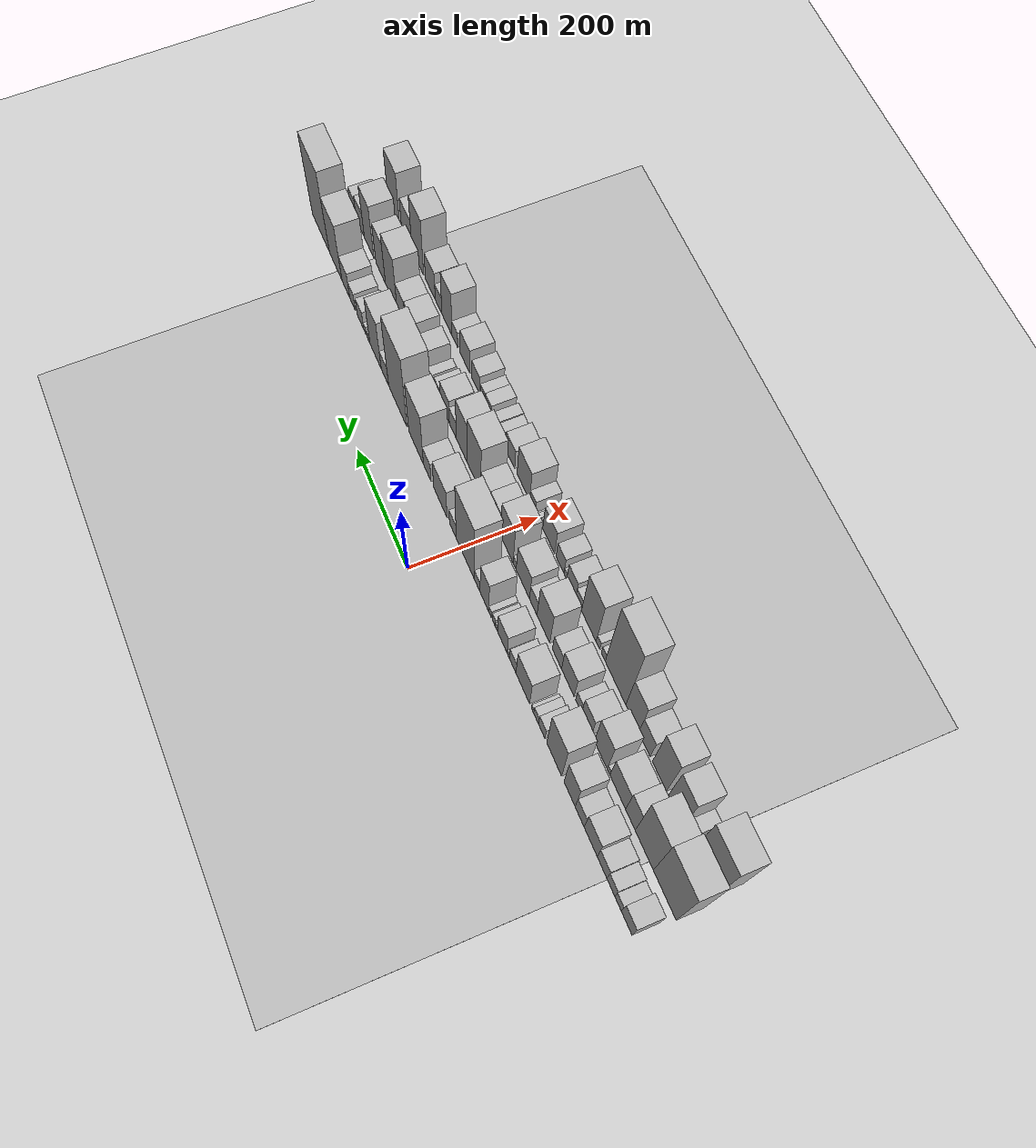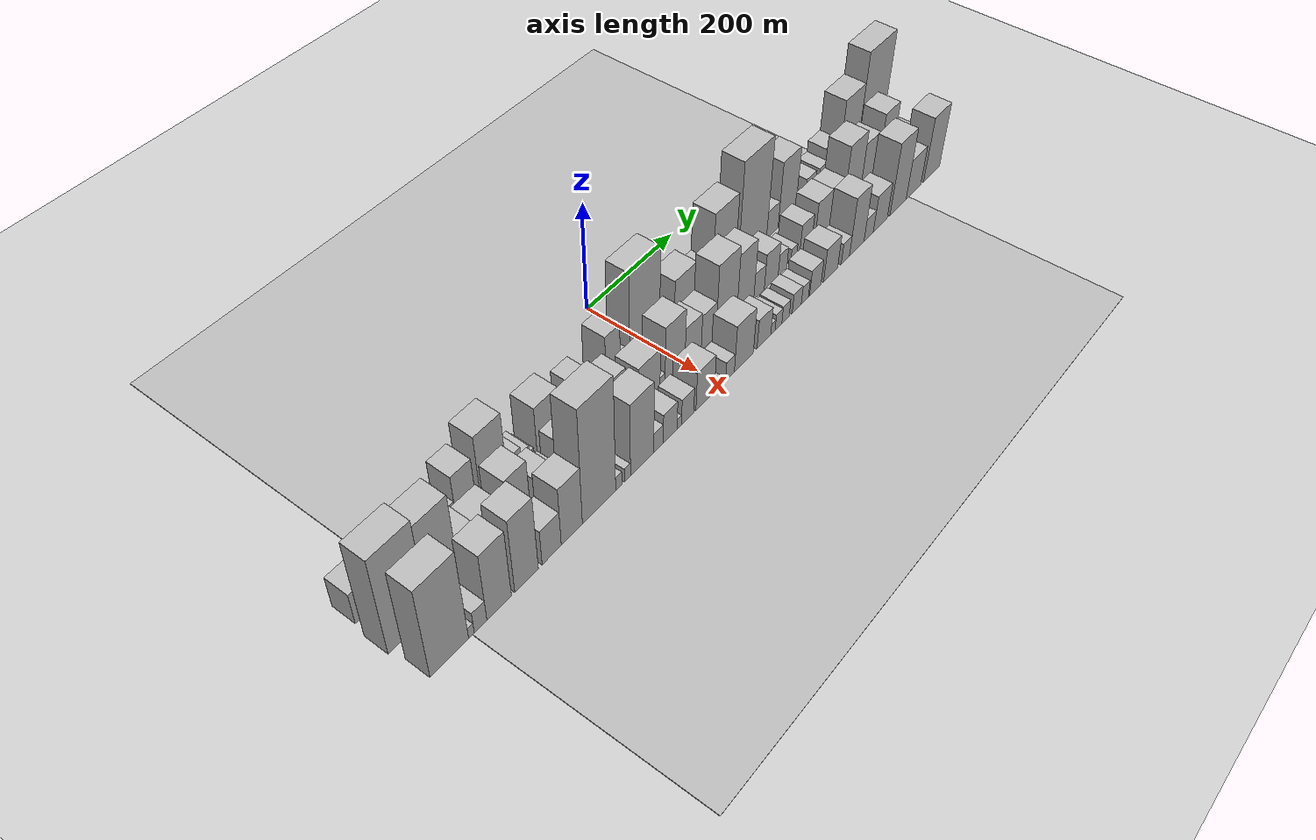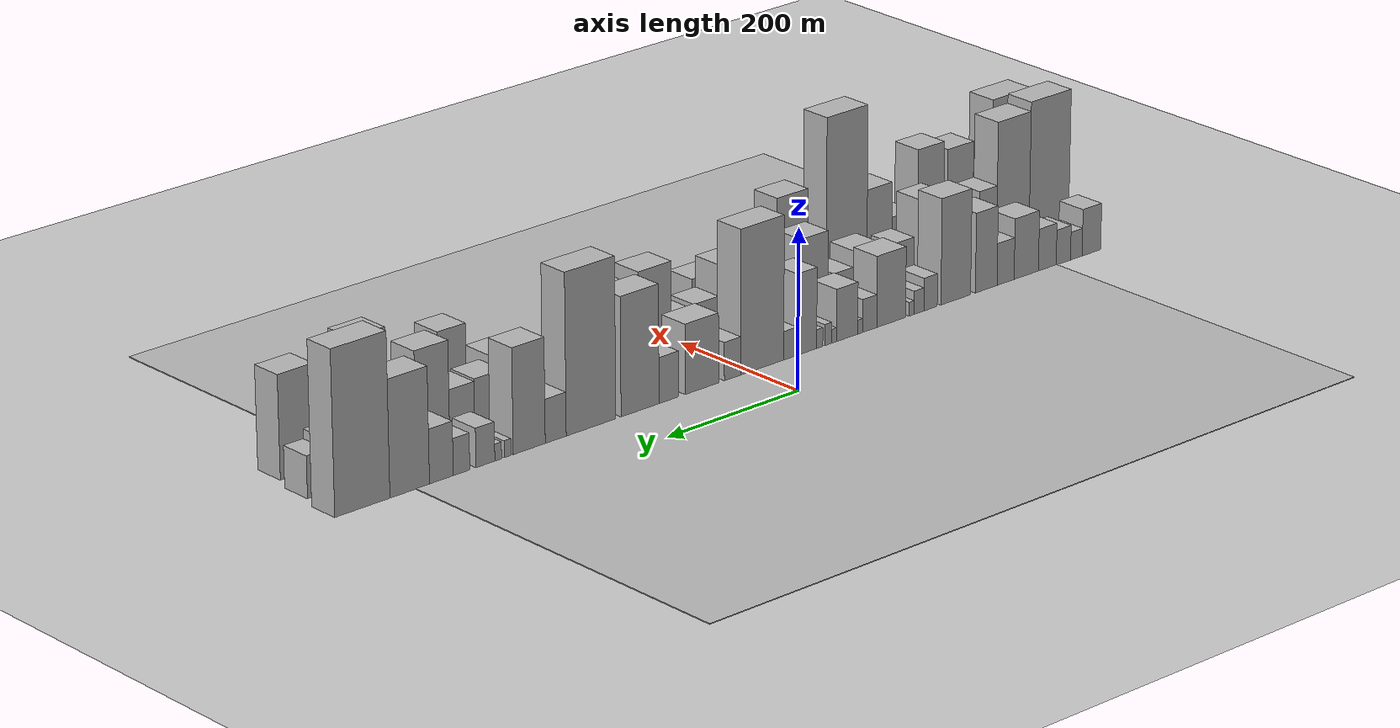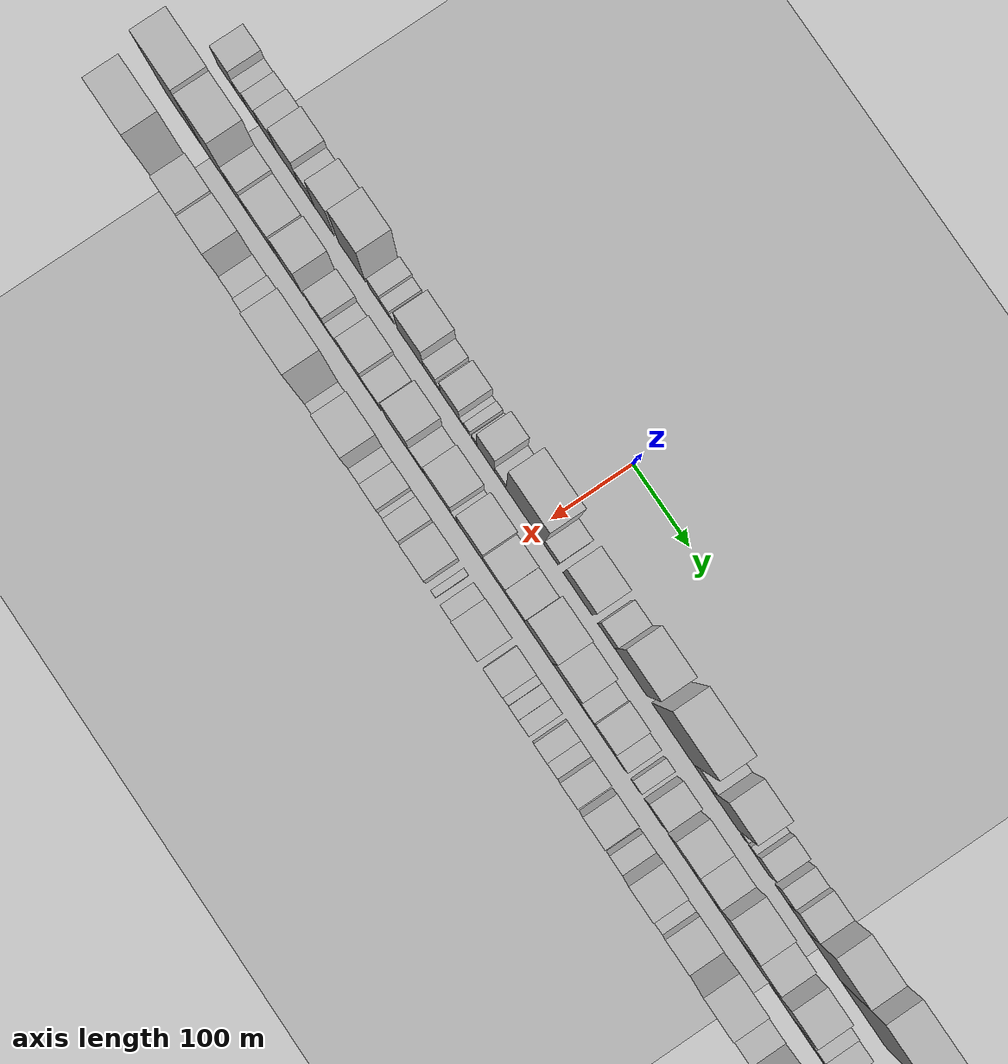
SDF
<?xml version="1.0" encoding="utf-8"?>

<sdf version="1.6">

   <world name="default">

      <gui fullscreen="0">

         <camera name="user_camera">

            <pose>-15 0 4.57585 0 0 0</pose>

            <view_controller>orbit</view_controller>

         </camera>

      </gui>

      <scene>

         <sky>

           <clouds>

             <speed>12</speed>

           </clouds>

         </sky>

         <ambient>0.4 0.4 0.4 1</ambient>

         <background>0.7 0.7 0.7 1</background>

         <shadows>1</shadows>

      </scene>

      <gravity>0 0 -9.8066</gravity>

      <magnetic_field>6e-06 2.3e-05 -4.2e-05</magnetic_field>

      <physics default="0" name="default_physics" type="ode">

         <ode>

            <solver>

               <type>quick</type>

               <iters>10</iters>

               <sor>1.0</sor>

               <use_dynamic_moi_rescaling>0</use_dynamic_moi_rescaling>

            </solver>

            <constraints>

               <cfm>0</cfm>

               <erp>0.2</erp>

               <contact_max_correcting_vel>100</contact_max_correcting_vel>

               <contact_surface_layer>0.001</contact_surface_layer>

            </constraints>

         </ode>

         <max_step_size>0.004</max_step_size>

         <real_time_factor>1</real_time_factor>

         <real_time_update_rate>250</real_time_update_rate>

      </physics>

      <light name="sun" type="directional">

         <cast_shadows>1</cast_shadows>

         <pose>0 0 10 0 0 0</pose>

         <diffuse>0.8 0.8 0.8 1</diffuse>

         <specular>0.2 0.2 0.2 1</specular>

         <attenuation>

            <range>1000</range>

            <constant>0.9</constant>

            <linear>0.01</linear>

            <quadratic>0.001</quadratic>

         </attenuation>

         <direction>-0.5 0.1 -0.9</direction>

      </light>

      <include>

         <name>ground_plane_1</name>

         <uri>model://HANNAS_ground_plane</uri>

         <pose>0 0 0  0 0 0</pose>

      </include>

      <include>

         <name>ground_plane_2</name>

         <uri>model://HANNAS_ground_plane</uri>

         <pose>100 0 0  0 0 0</pose>

      </include>

      <model name="building_1">

         <static>1</static>

         <pose frame="">100.0000 -558.9998 0 0.000000 0.000000 0.000000</pose>

         <link name="link">

            <pose frame="">0 0 30.00 0 0 0</pose>

            <collision name="collision">

               <geometry>

                  <box>

                     <size>40.0000 32.0005 60.0000</size>

                  </box>

               </geometry>

               <max_contacts>10</max_contacts>

               <surface>

                  <contact>

                     <ode/>

                  </contact>

                  <bounce/>

                  <friction>

                     <torsional>

                        <ode/>

                     </torsional>

                     <ode/>

                  </friction>

               </surface>

            </collision>

            <visual name="visual">

               <cast_shadows>0</cast_shadows>

               <geometry>

                  <box>

                     <size>40.0000 32.0005 60.0000</size>

                  </box>

               </geometry>

               <material>

                  <script>

                     <uri>model://HANNAS_wall/materials/scripts</uri>

                     <uri>model://HANNAS_wall/materials/textures</uri>

                     <name>vrc/HANNAS_wall</name>

                  </script>

               </material>

            </visual>

            <self_collide>0</self_collide>

            <enable_wind>0</enable_wind>

            <kinematic>0</kinematic>

         </link>

      </model>

      <model name="building_2">

         <static>1</static>

         <pose frame="">100.0000 -533.0357 0 0.000000 0.000000 0.000000</pose>

         <link name="link">

            <pose frame="">0 0 18.00 0 0 0</pose>

            <collision name="collision">

               <geometry>

                  <box>

                     <size>40.0000 19.9277 36.0000</size>

                  </box>

               </geometry>

               <max_contacts>10</max_contacts>

               <surface>

                  <contact>

                     <ode/>

                  </contact>

                  <bounce/>

                  <friction>

                     <torsional>

                        <ode/>

                     </torsional>

                     <ode/>

                  </friction>

               </surface>

            </collision>

            <visual name="visual">

               <cast_shadows>0</cast_shadows>

               <geometry>

                  <box>

                     <size>40.0000 19.9277 36.0000</size>

                  </box>

               </geometry>

               <material>

                  <script>

                     <uri>model://HANNAS_wall/materials/scripts</uri>

                     <uri>model://HANNAS_wall/materials/textures</uri>

                     <name>vrc/HANNAS_wall</name>

                  </script>

               </material>

            </visual>

            <self_collide>0</self_collide>

            <enable_wind>0</enable_wind>

            <kinematic>0</kinematic>

         </link>

      </model>

      <model name="building_3">

         <static>1</static>

         <pose frame="">100.0000 -510.8736 0 0.000000 0.000000 0.000000</pose>

         <link name="link">

            <pose frame="">0 0 22.50 0 0 0</pose>

            <collision name="collision">

               <geometry>

                  <box>

                     <size>40.0000 24.3965 45.0000</size>

                  </box>

               </geometry>

               <max_contacts>10</max_contacts>

               <surface>

                  <contact>

                     <ode/>

                  </contact>

                  <bounce/>

                  <friction>

                     <torsional>

                        <ode/>

                     </torsional>

                     <ode/>

                  </friction>

               </surface>

            </collision>

            <visual name="visual">

               <cast_shadows>0</cast_shadows>

               <geometry>

                  <box>

                     <size>40.0000 24.3965 45.0000</size>

                  </box>

               </geometry>

               <material>

                  <script>

                     <uri>model://HANNAS_wall/materials/scripts</uri>

                     <uri>model://HANNAS_wall/materials/textures</uri>

                     <name>vrc/HANNAS_wall</name>

                  </script>

               </material>

            </visual>

            <self_collide>0</self_collide>

            <enable_wind>0</enable_wind>

            <kinematic>0</kinematic>

         </link>

      </model>

      <model name="building_4">

         <static>1</static>

         <pose frame="">100.0000 -483.5138 0 0.000000 0.000000 0.000000</pose>

         <link name="link">

            <pose frame="">0 0 27.00 0 0 0</pose>

            <collision name="collision">

               <geometry>

                  <box>

                     <size>40.0000 30.3230 54.0000</size>

                  </box>

               </geometry>

               <max_contacts>10</max_contacts>

               <surface>

                  <contact>

                     <ode/>

                  </contact>

                  <bounce/>

                  <friction>

                     <torsional>

                        <ode/>

                     </torsional>

                     <ode/>

                  </friction>

               </surface>

            </collision>

            <visual name="visual">

               <cast_shadows>0</cast_shadows>

               <geometry>

                  <box>

                     <size>40.0000 30.3230 54.0000</size>

                  </box>

               </geometry>

               <material>

                  <script>

                     <uri>model://HANNAS_wall/materials/scripts</uri>

                     <uri>model://HANNAS_wall/materials/textures</uri>

                     <name>vrc/HANNAS_wall</name>

                  </script>

               </material>

            </visual>

            <self_collide>0</self_collide>

            <enable_wind>0</enable_wind>

            <kinematic>0</kinematic>

         </link>

      </model>

      <model name="building_5">

         <static>1</static>

         <pose frame="">100.0000 -447.7967 0 0.000000 0.000000 0.000000</pose>

         <link name="link">

            <pose frame="">0 0 39.00 0 0 0</pose>

            <collision name="collision">

               <geometry>

                  <box>

                     <size>40.0000 41.1111 78.0000</size>

                  </box>

               </geometry>

               <max_contacts>10</max_contacts>

               <surface>

                  <contact>

                     <ode/>

                  </contact>

                  <bounce/>

                  <friction>

                     <torsional>

                        <ode/>

                     </torsional>

                     <ode/>

                  </friction>

               </surface>

            </collision>

            <visual name="visual">

               <cast_shadows>0</cast_shadows>

               <geometry>

                  <box>

                     <size>40.0000 41.1111 78.0000</size>

                  </box>

               </geometry>

               <material>

                  <script>

                     <uri>model://HANNAS_wall/materials/scripts</uri>

                     <uri>model://HANNAS_wall/materials/textures</uri>

                     <name>vrc/HANNAS_wall</name>

                  </script>

               </material>

            </visual>

            <self_collide>0</self_collide>

            <enable_wind>0</enable_wind>

            <kinematic>0</kinematic>

         </link>

      </model>

      <model name="building_6">

         <static>1</static>

         <pose frame="">100.0000 -412.8341 0 0.000000 0.000000 0.000000</pose>

         <link name="link">

            <pose frame="">0 0 27.00 0 0 0</pose>

            <collision name="collision">

               <geometry>

                  <box>

                     <size>40.0000 28.8142 54.0000</size>

                  </box>

               </geometry>

               <max_contacts>10</max_contacts>

               <surface>

                  <contact>

                     <ode/>

                  </contact>

                  <bounce/>

                  <friction>

                     <torsional>

                        <ode/>

                     </torsional>

                     <ode/>

                  </friction>

               </surface>

            </collision>

            <visual name="visual">

               <cast_shadows>0</cast_shadows>

               <geometry>

                  <box>

                     <size>40.0000 28.8142 54.0000</size>

                  </box>

               </geometry>

               <material>

                  <script>

                     <uri>model://HANNAS_wall/materials/scripts</uri>

                     <uri>model://HANNAS_wall/materials/textures</uri>

                     <name>vrc/HANNAS_wall</name>

                  </script>

               </material>

            </visual>

            <self_collide>0</self_collide>

            <enable_wind>0</enable_wind>

            <kinematic>0</kinematic>

         </link>

      </model>

      <model name="building_7">

         <static>1</static>

         <pose frame="">100.0000 -380.3143 0 0.000000 0.000000 0.000000</pose>

         <link name="link">

            <pose frame="">0 0 51.00 0 0 0</pose>

            <collision name="collision">

               <geometry>

                  <box>

                     <size>40.0000 36.2254 102.0000</size>

                  </box>

               </geometry>

               <max_contacts>10</max_contacts>

               <surface>

                  <contact>

                     <ode/>

                  </contact>

                  <bounce/>

                  <friction>

                     <torsional>

                        <ode/>

                     </torsional>

                     <ode/>

                  </friction>

               </surface>

            </collision>

            <visual name="visual">

               <cast_shadows>0</cast_shadows>

               <geometry>

                  <box>

                     <size>40.0000 36.2254 102.0000</size>

                  </box>

               </geometry>

               <material>

                  <script>

                     <uri>model://HANNAS_wall/materials/scripts</uri>

                     <uri>model://HANNAS_wall/materials/textures</uri>

                     <name>vrc/HANNAS_wall</name>

                  </script>

               </material>

            </visual>

            <self_collide>0</self_collide>

            <enable_wind>0</enable_wind>

            <kinematic>0</kinematic>

         </link>

      </model>

      <model name="building_8">

         <static>1</static>

         <pose frame="">100.0000 -329.6145 0 0.000000 0.000000 0.000000</pose>

         <link name="link">

            <pose frame="">0 0 67.50 0 0 0</pose>

            <collision name="collision">

               <geometry>

                  <box>

                     <size>40.0000 49.1742 135.0000</size>

                  </box>

               </geometry>

               <max_contacts>10</max_contacts>

               <surface>

                  <contact>

                     <ode/>

                  </contact>

                  <bounce/>

                  <friction>

                     <torsional>

                        <ode/>

                     </torsional>

                     <ode/>

                  </friction>

               </surface>

            </collision>

            <visual name="visual">

               <cast_shadows>0</cast_shadows>

               <geometry>

                  <box>

                     <size>40.0000 49.1742 135.0000</size>

                  </box>

               </geometry>

               <material>

                  <script>

                     <uri>model://HANNAS_wall/materials/scripts</uri>

                     <uri>model://HANNAS_wall/materials/textures</uri>

                     <name>vrc/HANNAS_wall</name>

                  </script>

               </material>

            </visual>

            <self_collide>0</self_collide>

            <enable_wind>0</enable_wind>

            <kinematic>0</kinematic>

         </link>

      </model>

      <model name="building_9">

         <static>1</static>

         <pose frame="">100.0000 -288.0605 0 0.000000 0.000000 0.000000</pose>

         <link name="link">

            <pose frame="">0 0 21.00 0 0 0</pose>

            <collision name="collision">

               <geometry>

                  <box>

                     <size>40.0000 21.9337 42.0000</size>

                  </box>

               </geometry>

               <max_contacts>10</max_contacts>

               <surface>

                  <contact>

                     <ode/>

                  </contact>

                  <bounce/>

                  <friction>

                     <torsional>

                        <ode/>

                     </torsional>

                     <ode/>

                  </friction>

               </surface>

            </collision>

            <visual name="visual">

               <cast_shadows>0</cast_shadows>

               <geometry>

                  <box>

                     <size>40.0000 21.9337 42.0000</size>

                  </box>

               </geometry>

               <material>

                  <script>

                     <uri>model://HANNAS_wall/materials/scripts</uri>

                     <uri>model://HANNAS_wall/materials/textures</uri>

                     <name>vrc/HANNAS_wall</name>

                  </script>

               </material>

            </visual>

            <self_collide>0</self_collide>

            <enable_wind>0</enable_wind>

            <kinematic>0</kinematic>

         </link>

      </model>

      <model name="building_10">

         <static>1</static>

         <pose frame="">100.0000 -269.0830 0 0.000000 0.000000 0.000000</pose>

         <link name="link">

            <pose frame="">0 0 15.00 0 0 0</pose>

            <collision name="collision">

               <geometry>

                  <box>

                     <size>40.0000 16.0212 30.0000</size>

                  </box>

               </geometry>

               <max_contacts>10</max_contacts>

               <surface>

                  <contact>

                     <ode/>

                  </contact>

                  <bounce/>

                  <friction>

                     <torsional>

                        <ode/>

                     </torsional>

                     <ode/>

                  </friction>

               </surface>

            </collision>

            <visual name="visual">

               <cast_shadows>0</cast_shadows>

               <geometry>

                  <box>

                     <size>40.0000 16.0212 30.0000</size>

                  </box>

               </geometry>

               <material>

                  <script>

                     <uri>model://HANNAS_wall/materials/scripts</uri>

                     <uri>model://HANNAS_wall/materials/textures</uri>

                     <name>vrc/HANNAS_wall</name>

                  </script>

               </material>

            </visual>

            <self_collide>0</self_collide>

            <enable_wind>0</enable_wind>

            <kinematic>0</kinematic>

         </link>

      </model>

      <model name="building_11">

         <static>1</static>

         <pose frame="">100.0000 -257.0660 0 0.000000 0.000000 0.000000</pose>

         <link name="link">

            <pose frame="">0 0 9.00 0 0 0</pose>

            <collision name="collision">

               <geometry>

                  <box>

                     <size>40.0000 8.0128 18.0000</size>

                  </box>

               </geometry>

               <max_contacts>10</max_contacts>

               <surface>

                  <contact>

                     <ode/>

                  </contact>

                  <bounce/>

                  <friction>

                     <torsional>

                        <ode/>

                     </torsional>

                     <ode/>

                  </friction>

               </surface>

            </collision>

            <visual name="visual">

               <cast_shadows>0</cast_shadows>

               <geometry>

                  <box>

                     <size>40.0000 8.0128 18.0000</size>

                  </box>

               </geometry>

               <material>

                  <script>

                     <uri>model://HANNAS_wall/materials/scripts</uri>

                     <uri>model://HANNAS_wall/materials/textures</uri>

                     <name>vrc/HANNAS_wall</name>

                  </script>

               </material>

            </visual>

            <self_collide>0</self_collide>

            <enable_wind>0</enable_wind>

            <kinematic>0</kinematic>

         </link>

      </model>

      <model name="building_12">

         <static>1</static>

         <pose frame="">100.0000 -223.5987 0 0.000000 0.000000 0.000000</pose>

         <link name="link">

            <pose frame="">0 0 45.00 0 0 0</pose>

            <collision name="collision">

               <geometry>

                  <box>

                     <size>40.0000 46.9219 90.0000</size>

                  </box>

               </geometry>

               <max_contacts>10</max_contacts>

               <surface>

                  <contact>

                     <ode/>

                  </contact>

                  <bounce/>

                  <friction>

                     <torsional>

                        <ode/>

                     </torsional>

                     <ode/>

                  </friction>

               </surface>

            </collision>

            <visual name="visual">

               <cast_shadows>0</cast_shadows>

               <geometry>

                  <box>

                     <size>40.0000 46.9219 90.0000</size>

                  </box>

               </geometry>

               <material>

                  <script>

                     <uri>model://HANNAS_wall/materials/scripts</uri>

                     <uri>model://HANNAS_wall/materials/textures</uri>

                     <name>vrc/HANNAS_wall</name>

                  </script>

               </material>

            </visual>

            <self_collide>0</self_collide>

            <enable_wind>0</enable_wind>

            <kinematic>0</kinematic>

         </link>

      </model>

      <model name="building_13">

         <static>1</static>

         <pose frame="">100.0000 -188.6355 0 0.000000 0.000000 0.000000</pose>

         <link name="link">

            <pose frame="">0 0 21.00 0 0 0</pose>

            <collision name="collision">

               <geometry>

                  <box>

                     <size>40.0000 23.0045 42.0000</size>

                  </box>

               </geometry>

               <max_contacts>10</max_contacts>

               <surface>

                  <contact>

                     <ode/>

                  </contact>

                  <bounce/>

                  <friction>

                     <torsional>

                        <ode/>

                     </torsional>

                     <ode/>

                  </friction>

               </surface>

            </collision>

            <visual name="visual">

               <cast_shadows>0</cast_shadows>

               <geometry>

                  <box>

                     <size>40.0000 23.0045 42.0000</size>

                  </box>

               </geometry>

               <material>

                  <script>

                     <uri>model://HANNAS_wall/materials/scripts</uri>

                     <uri>model://HANNAS_wall/materials/textures</uri>

                     <name>vrc/HANNAS_wall</name>

                  </script>

               </material>

            </visual>

            <self_collide>0</self_collide>

            <enable_wind>0</enable_wind>

            <kinematic>0</kinematic>

         </link>

      </model>

      <model name="building_14">

         <static>1</static>

         <pose frame="">100.0000 -173.3372 0 0.000000 0.000000 0.000000</pose>

         <link name="link">

            <pose frame="">0 0 9.00 0 0 0</pose>

            <collision name="collision">

               <geometry>

                  <box>

                     <size>40.0000 7.5920 18.0000</size>

                  </box>

               </geometry>

               <max_contacts>10</max_contacts>

               <surface>

                  <contact>

                     <ode/>

                  </contact>

                  <bounce/>

                  <friction>

                     <torsional>

                        <ode/>

                     </torsional>

                     <ode/>

                  </friction>

               </surface>

            </collision>

            <visual name="visual">

               <cast_shadows>0</cast_shadows>

               <geometry>

                  <box>

                     <size>40.0000 7.5920 18.0000</size>

                  </box>

               </geometry>

               <material>

                  <script>

                     <uri>model://HANNAS_wall/materials/scripts</uri>

                     <uri>model://HANNAS_wall/materials/textures</uri>

                     <name>vrc/HANNAS_wall</name>

                  </script>

               </material>

            </visual>

            <self_collide>0</self_collide>

            <enable_wind>0</enable_wind>

            <kinematic>0</kinematic>

         </link>

      </model>

      <model name="building_15">

         <static>1</static>

         <pose frame="">100.0000 -152.3897 0 0.000000 0.000000 0.000000</pose>

         <link name="link">

            <pose frame="">0 0 33.00 0 0 0</pose>

            <collision name="collision">

               <geometry>

                  <box>

                     <size>40.0000 34.3029 66.0000</size>

                  </box>

               </geometry>

               <max_contacts>10</max_contacts>

               <surface>

                  <contact>

                     <ode/>

                  </contact>

                  <bounce/>

                  <friction>

                     <torsional>

                        <ode/>

                     </torsional>

                     <ode/>

                  </friction>

               </surface>

            </collision>

            <visual name="visual">

               <cast_shadows>0</cast_shadows>

               <geometry>

                  <box>

                     <size>40.0000 34.3029 66.0000</size>

                  </box>

               </geometry>

               <material>

                  <script>

                     <uri>model://HANNAS_wall/materials/scripts</uri>

                     <uri>model://HANNAS_wall/materials/textures</uri>

                     <name>vrc/HANNAS_wall</name>

                  </script>

               </material>

            </visual>

            <self_collide>0</self_collide>

            <enable_wind>0</enable_wind>

            <kinematic>0</kinematic>

         </link>

      </model>

      <model name="building_16">

         <static>1</static>

         <pose frame="">100.0000 -131.3970 0 0.000000 0.000000 0.000000</pose>

         <link name="link">

            <pose frame="">0 0 9.00 0 0 0</pose>

            <collision name="collision">

               <geometry>

                  <box>

                     <size>40.0000 7.6826 18.0000</size>

                  </box>

               </geometry>

               <max_contacts>10</max_contacts>

               <surface>

                  <contact>

                     <ode/>

                  </contact>

                  <bounce/>

                  <friction>

                     <torsional>

                        <ode/>

                     </torsional>

                     <ode/>

                  </friction>

               </surface>

            </collision>

            <visual name="visual">

               <cast_shadows>0</cast_shadows>

               <geometry>

                  <box>

                     <size>40.0000 7.6826 18.0000</size>

                  </box>

               </geometry>

               <material>

                  <script>

                     <uri>model://HANNAS_wall/materials/scripts</uri>

                     <uri>model://HANNAS_wall/materials/textures</uri>

                     <name>vrc/HANNAS_wall</name>

                  </script>

               </material>

            </visual>

            <self_collide>0</self_collide>

            <enable_wind>0</enable_wind>

            <kinematic>0</kinematic>

         </link>

      </model>

      <model name="building_17">

         <static>1</static>

         <pose frame="">100.0000 -121.9993 0 0.000000 0.000000 0.000000</pose>

         <link name="link">

            <pose frame="">0 0 13.50 0 0 0</pose>

            <collision name="collision">

               <geometry>

                  <box>

                     <size>40.0000 11.1128 27.0000</size>

                  </box>

               </geometry>

               <max_contacts>10</max_contacts>

               <surface>

                  <contact>

                     <ode/>

                  </contact>

                  <bounce/>

                  <friction>

                     <torsional>

                        <ode/>

                     </torsional>

                     <ode/>

                  </friction>

               </surface>

            </collision>

            <visual name="visual">

               <cast_shadows>0</cast_shadows>

               <geometry>

                  <box>

                     <size>40.0000 11.1128 27.0000</size>

                  </box>

               </geometry>

               <material>

                  <script>

                     <uri>model://HANNAS_wall/materials/scripts</uri>

                     <uri>model://HANNAS_wall/materials/textures</uri>

                     <name>vrc/HANNAS_wall</name>

                  </script>

               </material>

            </visual>

            <self_collide>0</self_collide>

            <enable_wind>0</enable_wind>

            <kinematic>0</kinematic>

         </link>

      </model>

      <model name="building_18">

         <static>1</static>

         <pose frame="">100.0000 -108.5915 0 0.000000 0.000000 0.000000</pose>

         <link name="link">

            <pose frame="">0 0 12.00 0 0 0</pose>

            <collision name="collision">

               <geometry>

                  <box>

                     <size>40.0000 9.7029 24.0000</size>

                  </box>

               </geometry>

               <max_contacts>10</max_contacts>

               <surface>

                  <contact>

                     <ode/>

                  </contact>

                  <bounce/>

                  <friction>

                     <torsional>

                        <ode/>

                     </torsional>

                     <ode/>

                  </friction>

               </surface>

            </collision>

            <visual name="visual">

               <cast_shadows>0</cast_shadows>

               <geometry>

                  <box>

                     <size>40.0000 9.7029 24.0000</size>

                  </box>

               </geometry>

               <material>

                  <script>

                     <uri>model://HANNAS_wall/materials/scripts</uri>

                     <uri>model://HANNAS_wall/materials/textures</uri>

                     <name>vrc/HANNAS_wall</name>

                  </script>

               </material>

            </visual>

            <self_collide>0</self_collide>

            <enable_wind>0</enable_wind>

            <kinematic>0</kinematic>

         </link>

      </model>

      <model name="building_19">

         <static>1</static>

         <pose frame="">100.0000 -88.0765 0 0.000000 0.000000 0.000000</pose>

         <link name="link">

            <pose frame="">0 0 51.00 0 0 0</pose>

            <collision name="collision">

               <geometry>

                  <box>

                     <size>40.0000 31.3270 102.0000</size>

                  </box>

               </geometry>

               <max_contacts>10</max_contacts>

               <surface>

                  <contact>

                     <ode/>

                  </contact>

                  <bounce/>

                  <friction>

                     <torsional>

                        <ode/>

                     </torsional>

                     <ode/>

                  </friction>

               </surface>

            </collision>

            <visual name="visual">

               <cast_shadows>0</cast_shadows>

               <geometry>

                  <box>

                     <size>40.0000 31.3270 102.0000</size>

                  </box>

               </geometry>

               <material>

                  <script>

                     <uri>model://HANNAS_wall/materials/scripts</uri>

                     <uri>model://HANNAS_wall/materials/textures</uri>

                     <name>vrc/HANNAS_wall</name>

                  </script>

               </material>

            </visual>

            <self_collide>0</self_collide>

            <enable_wind>0</enable_wind>

            <kinematic>0</kinematic>

         </link>

      </model>

      <model name="building_20">

         <static>1</static>

         <pose frame="">100.0000 -62.0371 0 0.000000 0.000000 0.000000</pose>

         <link name="link">

            <pose frame="">0 0 18.00 0 0 0</pose>

            <collision name="collision">

               <geometry>

                  <box>

                     <size>40.0000 20.7519 36.0000</size>

                  </box>

               </geometry>

               <max_contacts>10</max_contacts>

               <surface>

                  <contact>

                     <ode/>

                  </contact>

                  <bounce/>

                  <friction>

                     <torsional>

                        <ode/>

                     </torsional>

                     <ode/>

                  </friction>

               </surface>

            </collision>

            <visual name="visual">

               <cast_shadows>0</cast_shadows>

               <geometry>

                  <box>

                     <size>40.0000 20.7519 36.0000</size>

                  </box>

               </geometry>

               <material>

                  <script>

                     <uri>model://HANNAS_wall/materials/scripts</uri>

                     <uri>model://HANNAS_wall/materials/textures</uri>

                     <name>vrc/HANNAS_wall</name>

                  </script>

               </material>

            </visual>

            <self_collide>0</self_collide>

            <enable_wind>0</enable_wind>

            <kinematic>0</kinematic>

         </link>

      </model>

      <model name="building_21">

         <static>1</static>

         <pose frame="">100.0000 -17.9185 0 0.000000 0.000000 0.000000</pose>

         <link name="link">

            <pose frame="">0 0 90.00 0 0 0</pose>

            <collision name="collision">

               <geometry>

                  <box>

                     <size>40.0000 67.4853 180.0000</size>

                  </box>

               </geometry>

               <max_contacts>10</max_contacts>

               <surface>

                  <contact>

                     <ode/>

                  </contact>

                  <bounce/>

                  <friction>

                     <torsional>

                        <ode/>

                     </torsional>

                     <ode/>

                  </friction>

               </surface>

            </collision>

            <visual name="visual">

               <cast_shadows>0</cast_shadows>

               <geometry>

                  <box>

                     <size>40.0000 67.4853 180.0000</size>

                  </box>

               </geometry>

               <material>

                  <script>

                     <uri>model://HANNAS_wall/materials/scripts</uri>

                     <uri>model://HANNAS_wall/materials/textures</uri>

                     <name>vrc/HANNAS_wall</name>

                  </script>

               </material>

            </visual>

            <self_collide>0</self_collide>

            <enable_wind>0</enable_wind>

            <kinematic>0</kinematic>

         </link>

      </model>

      <model name="building_22">

         <static>1</static>

         <pose frame="">100.0000 28.6319 0 0.000000 0.000000 0.000000</pose>

         <link name="link">

            <pose frame="">0 0 24.00 0 0 0</pose>

            <collision name="collision">

               <geometry>

                  <box>

                     <size>40.0000 25.6156 48.0000</size>

                  </box>

               </geometry>

               <max_contacts>10</max_contacts>

               <surface>

                  <contact>

                     <ode/>

                  </contact>

                  <bounce/>

                  <friction>

                     <torsional>

                        <ode/>

                     </torsional>

                     <ode/>

                  </friction>

               </surface>

            </collision>

            <visual name="visual">

               <cast_shadows>0</cast_shadows>

               <geometry>

                  <box>

                     <size>40.0000 25.6156 48.0000</size>

                  </box>

               </geometry>

               <material>

                  <script>

                     <uri>model://HANNAS_wall/materials/scripts</uri>

                     <uri>model://HANNAS_wall/materials/textures</uri>

                     <name>vrc/HANNAS_wall</name>

                  </script>

               </material>

            </visual>

            <self_collide>0</self_collide>

            <enable_wind>0</enable_wind>

            <kinematic>0</kinematic>

         </link>

      </model>

      <model name="building_23">

         <static>1</static>

         <pose frame="">100.0000 76.1748 0 0.000000 0.000000 0.000000</pose>

         <link name="link">

            <pose frame="">0 0 43.50 0 0 0</pose>

            <collision name="collision">

               <geometry>

                  <box>

                     <size>40.0000 51.4701 87.0000</size>

                  </box>

               </geometry>

               <max_contacts>10</max_contacts>

               <surface>

                  <contact>

                     <ode/>

                  </contact>

                  <bounce/>

                  <friction>

                     <torsional>

                        <ode/>

                     </torsional>

                     <ode/>

                  </friction>

               </surface>

            </collision>

            <visual name="visual">

               <cast_shadows>0</cast_shadows>

               <geometry>

                  <box>

                     <size>40.0000 51.4701 87.0000</size>

                  </box>

               </geometry>

               <material>

                  <script>

                     <uri>model://HANNAS_wall/materials/scripts</uri>

                     <uri>model://HANNAS_wall/materials/textures</uri>

                     <name>vrc/HANNAS_wall</name>

                  </script>

               </material>

            </visual>

            <self_collide>0</self_collide>

            <enable_wind>0</enable_wind>

            <kinematic>0</kinematic>

         </link>

      </model>

      <model name="building_24">

         <static>1</static>

         <pose frame="">100.0000 126.9499 0 0.000000 0.000000 0.000000</pose>

         <link name="link">

            <pose frame="">0 0 28.50 0 0 0</pose>

            <collision name="collision">

               <geometry>

                  <box>

                     <size>40.0000 30.0802 57.0000</size>

                  </box>

               </geometry>

               <max_contacts>10</max_contacts>

               <surface>

                  <contact>

                     <ode/>

                  </contact>

                  <bounce/>

                  <friction>

                     <torsional>

                        <ode/>

                     </torsional>

                     <ode/>

                  </friction>

               </surface>

            </collision>

            <visual name="visual">

               <cast_shadows>0</cast_shadows>

               <geometry>

                  <box>

                     <size>40.0000 30.0802 57.0000</size>

                  </box>

               </geometry>

               <material>

                  <script>

                     <uri>model://HANNAS_wall/materials/scripts</uri>

                     <uri>model://HANNAS_wall/materials/textures</uri>

                     <name>vrc/HANNAS_wall</name>

                  </script>

               </material>

            </visual>

            <self_collide>0</self_collide>

            <enable_wind>0</enable_wind>

            <kinematic>0</kinematic>

         </link>

      </model>

      <model name="building_25">

         <static>1</static>

         <pose frame="">100.0000 170.7572 0 0.000000 0.000000 0.000000</pose>

         <link name="link">

            <pose frame="">0 0 73.50 0 0 0</pose>

            <collision name="collision">

               <geometry>

                  <box>

                     <size>40.0000 57.5343 147.0000</size>

                  </box>

               </geometry>

               <max_contacts>10</max_contacts>

               <surface>

                  <contact>

                     <ode/>

                  </contact>

                  <bounce/>

                  <friction>

                     <torsional>

                        <ode/>

                     </torsional>

                     <ode/>

                  </friction>

               </surface>

            </collision>

            <visual name="visual">

               <cast_shadows>0</cast_shadows>

               <geometry>

                  <box>

                     <size>40.0000 57.5343 147.0000</size>

                  </box>

               </geometry>

               <material>

                  <script>

                     <uri>model://HANNAS_wall/materials/scripts</uri>

                     <uri>model://HANNAS_wall/materials/textures</uri>

                     <name>vrc/HANNAS_wall</name>

                  </script>

               </material>

            </visual>

            <self_collide>0</self_collide>

            <enable_wind>0</enable_wind>

            <kinematic>0</kinematic>

         </link>

      </model>

      <model name="building_26">

         <static>1</static>

         <pose frame="">100.0000 244.5713 0 0.000000 0.000000 0.000000</pose>

         <link name="link">

            <pose frame="">0 0 99.00 0 0 0</pose>

            <collision name="collision">

               <geometry>

                  <box>

                     <size>40.0000 74.0940 198.0000</size>

                  </box>

               </geometry>

               <max_contacts>10</max_contacts>

               <surface>

                  <contact>

                     <ode/>

                  </contact>

                  <bounce/>

                  <friction>

                     <torsional>

                        <ode/>

                     </torsional>

                     <ode/>

                  </friction>

               </surface>

            </collision>

            <visual name="visual">

               <cast_shadows>0</cast_shadows>

               <geometry>

                  <box>

                     <size>40.0000 74.0940 198.0000</size>

                  </box>

               </geometry>

               <material>

                  <script>

                     <uri>model://HANNAS_wall/materials/scripts</uri>

                     <uri>model://HANNAS_wall/materials/textures</uri>

                     <name>vrc/HANNAS_wall</name>

                  </script>

               </material>

            </visual>

            <self_collide>0</self_collide>

            <enable_wind>0</enable_wind>

            <kinematic>0</kinematic>

         </link>

      </model>

      <model name="building_27">

         <static>1</static>

         <pose frame="">100.0000 297.1448 0 0.000000 0.000000 0.000000</pose>

         <link name="link">

            <pose frame="">0 0 27.00 0 0 0</pose>

            <collision name="collision">

               <geometry>

                  <box>

                     <size>40.0000 31.0529 54.0000</size>

                  </box>

               </geometry>

               <max_contacts>10</max_contacts>

               <surface>

                  <contact>

                     <ode/>

                  </contact>

                  <bounce/>

                  <friction>

                     <torsional>

                        <ode/>

                     </torsional>

                     <ode/>

                  </friction>

               </surface>

            </collision>

            <visual name="visual">

               <cast_shadows>0</cast_shadows>

               <geometry>

                  <box>

                     <size>40.0000 31.0529 54.0000</size>

                  </box>

               </geometry>

               <material>

                  <script>

                     <uri>model://HANNAS_wall/materials/scripts</uri>

                     <uri>model://HANNAS_wall/materials/textures</uri>

                     <name>vrc/HANNAS_wall</name>

                  </script>

               </material>

            </visual>

            <self_collide>0</self_collide>

            <enable_wind>0</enable_wind>

            <kinematic>0</kinematic>

         </link>

      </model>

      <model name="building_28">

         <static>1</static>

         <pose frame="">100.0000 336.2664 0 0.000000 0.000000 0.000000</pose>

         <link name="link">

            <pose frame="">0 0 64.50 0 0 0</pose>

            <collision name="collision">

               <geometry>

                  <box>

                     <size>40.0000 47.1902 129.0000</size>

                  </box>

               </geometry>

               <max_contacts>10</max_contacts>

               <surface>

                  <contact>

                     <ode/>

                  </contact>

                  <bounce/>

                  <friction>

                     <torsional>

                        <ode/>

                     </torsional>

                     <ode/>

                  </friction>

               </surface>

            </collision>

            <visual name="visual">

               <cast_shadows>0</cast_shadows>

               <geometry>

                  <box>

                     <size>40.0000 47.1902 129.0000</size>

                  </box>

               </geometry>

               <material>

                  <script>

                     <uri>model://HANNAS_wall/materials/scripts</uri>

                     <uri>model://HANNAS_wall/materials/textures</uri>

                     <name>vrc/HANNAS_wall</name>

                  </script>

               </material>

            </visual>

            <self_collide>0</self_collide>

            <enable_wind>0</enable_wind>

            <kinematic>0</kinematic>

         </link>

      </model>

      <model name="building_29">

         <static>1</static>

         <pose frame="">100.0000 367.8762 0 0.000000 0.000000 0.000000</pose>

         <link name="link">

            <pose frame="">0 0 10.50 0 0 0</pose>

            <collision name="collision">

               <geometry>

                  <box>

                     <size>40.0000 10.0294 21.0000</size>

                  </box>

               </geometry>

               <max_contacts>10</max_contacts>

               <surface>

                  <contact>

                     <ode/>

                  </contact>

                  <bounce/>

                  <friction>

                     <torsional>

                        <ode/>

                     </torsional>

                     <ode/>

                  </friction>

               </surface>

            </collision>

            <visual name="visual">

               <cast_shadows>0</cast_shadows>

               <geometry>

                  <box>

                     <size>40.0000 10.0294 21.0000</size>

                  </box>

               </geometry>

               <material>

                  <script>

                     <uri>model://HANNAS_wall/materials/scripts</uri>

                     <uri>model://HANNAS_wall/materials/textures</uri>

                     <name>vrc/HANNAS_wall</name>

                  </script>

               </material>

            </visual>

            <self_collide>0</self_collide>

            <enable_wind>0</enable_wind>

            <kinematic>0</kinematic>

         </link>

      </model>

      <model name="building_30">

         <static>1</static>

         <pose frame="">100.0000 381.7923 0 0.000000 0.000000 0.000000</pose>

         <link name="link">

            <pose frame="">0 0 10.50 0 0 0</pose>

            <collision name="collision">

               <geometry>

                  <box>

                     <size>40.0000 9.8028 21.0000</size>

                  </box>

               </geometry>

               <max_contacts>10</max_contacts>

               <surface>

                  <contact>

                     <ode/>

                  </contact>

                  <bounce/>

                  <friction>

                     <torsional>

                        <ode/>

                     </torsional>

                     <ode/>

                  </friction>

               </surface>

            </collision>

            <visual name="visual">

               <cast_shadows>0</cast_shadows>

               <geometry>

                  <box>

                     <size>40.0000 9.8028 21.0000</size>

                  </box>

               </geometry>

               <material>

                  <script>

                     <uri>model://HANNAS_wall/materials/scripts</uri>

                     <uri>model://HANNAS_wall/materials/textures</uri>

                     <name>vrc/HANNAS_wall</name>

                  </script>

               </material>

            </visual>

            <self_collide>0</self_collide>

            <enable_wind>0</enable_wind>

            <kinematic>0</kinematic>

         </link>

      </model>

      <model name="building_31">

         <static>1</static>

         <pose frame="">100.0000 400.4193 0 0.000000 0.000000 0.000000</pose>

         <link name="link">

            <pose frame="">0 0 24.00 0 0 0</pose>

            <collision name="collision">

               <geometry>

                  <box>

                     <size>40.0000 27.4510 48.0000</size>

                  </box>

               </geometry>

               <max_contacts>10</max_contacts>

               <surface>

                  <contact>

                     <ode/>

                  </contact>

                  <bounce/>

                  <friction>

                     <torsional>

                        <ode/>

                     </torsional>

                     <ode/>

                  </friction>

               </surface>

            </collision>

            <visual name="visual">

               <cast_shadows>0</cast_shadows>

               <geometry>

                  <box>

                     <size>40.0000 27.4510 48.0000</size>

                  </box>

               </geometry>

               <material>

                  <script>

                     <uri>model://HANNAS_wall/materials/scripts</uri>

                     <uri>model://HANNAS_wall/materials/textures</uri>

                     <name>vrc/HANNAS_wall</name>

                  </script>

               </material>

            </visual>

            <self_collide>0</self_collide>

            <enable_wind>0</enable_wind>

            <kinematic>0</kinematic>

         </link>

      </model>

      <model name="building_32">

         <static>1</static>

         <pose frame="">100.0000 435.0461 0 0.000000 0.000000 0.000000</pose>

         <link name="link">

            <pose frame="">0 0 22.50 0 0 0</pose>

            <collision name="collision">

               <geometry>

                  <box>

                     <size>40.0000 23.8027 45.0000</size>

                  </box>

               </geometry>

               <max_contacts>10</max_contacts>

               <surface>

                  <contact>

                     <ode/>

                  </contact>

                  <bounce/>

                  <friction>

                     <torsional>

                        <ode/>

                     </torsional>

                     <ode/>

                  </friction>

               </surface>

            </collision>

            <visual name="visual">

               <cast_shadows>0</cast_shadows>

               <geometry>

                  <box>

                     <size>40.0000 23.8027 45.0000</size>

                  </box>

               </geometry>

               <material>

                  <script>

                     <uri>model://HANNAS_wall/materials/scripts</uri>

                     <uri>model://HANNAS_wall/materials/textures</uri>

                     <name>vrc/HANNAS_wall</name>

                  </script>

               </material>

            </visual>

            <self_collide>0</self_collide>

            <enable_wind>0</enable_wind>

            <kinematic>0</kinematic>

         </link>

      </model>

      <model name="building_33">

         <static>1</static>

         <pose frame="">100.0000 464.0478 0 0.000000 0.000000 0.000000</pose>

         <link name="link">

            <pose frame="">0 0 33.00 0 0 0</pose>

            <collision name="collision">

               <geometry>

                  <box>

                     <size>40.0000 34.2007 66.0000</size>

                  </box>

               </geometry>

               <max_contacts>10</max_contacts>

               <surface>

                  <contact>

                     <ode/>

                  </contact>

                  <bounce/>

                  <friction>

                     <torsional>

                        <ode/>

                     </torsional>

                     <ode/>

                  </friction>

               </surface>

            </collision>

            <visual name="visual">

               <cast_shadows>0</cast_shadows>

               <geometry>

                  <box>

                     <size>40.0000 34.2007 66.0000</size>

                  </box>

               </geometry>

               <material>

                  <script>

                     <uri>model://HANNAS_wall/materials/scripts</uri>

                     <uri>model://HANNAS_wall/materials/textures</uri>

                     <name>vrc/HANNAS_wall</name>

                  </script>

               </material>

            </visual>

            <self_collide>0</self_collide>

            <enable_wind>0</enable_wind>

            <kinematic>0</kinematic>

         </link>

      </model>

      <model name="building_34">

         <static>1</static>

         <pose frame="">100.0000 509.3301 0 0.000000 0.000000 0.000000</pose>

         <link name="link">

            <pose frame="">0 0 70.50 0 0 0</pose>

            <collision name="collision">

               <geometry>

                  <box>

                     <size>40.0000 56.3638 141.0000</size>

                  </box>

               </geometry>

               <max_contacts>10</max_contacts>

               <surface>

                  <contact>

                     <ode/>

                  </contact>

                  <bounce/>

                  <friction>

                     <torsional>

                        <ode/>

                     </torsional>

                     <ode/>

                  </friction>

               </surface>

            </collision>

            <visual name="visual">

               <cast_shadows>0</cast_shadows>

               <geometry>

                  <box>

                     <size>40.0000 56.3638 141.0000</size>

                  </box>

               </geometry>

               <material>

                  <script>

                     <uri>model://HANNAS_wall/materials/scripts</uri>

                     <uri>model://HANNAS_wall/materials/textures</uri>

                     <name>vrc/HANNAS_wall</name>

                  </script>

               </material>

            </visual>

            <self_collide>0</self_collide>

            <enable_wind>0</enable_wind>

            <kinematic>0</kinematic>

         </link>

      </model>

      <model name="building_35">

         <static>1</static>

         <pose frame="">100.0000 576.3049 0 0.000000 0.000000 0.000000</pose>

         <link name="link">

            <pose frame="">0 0 99.00 0 0 0</pose>

            <collision name="collision">

               <geometry>

                  <box>

                     <size>40.0000 77.5858 198.0000</size>

                  </box>

               </geometry>

               <max_contacts>10</max_contacts>

               <surface>

                  <contact>

                     <ode/>

                  </contact>

                  <bounce/>

                  <friction>

                     <torsional>

                        <ode/>

                     </torsional>

                     <ode/>

                  </friction>

               </surface>

            </collision>

            <visual name="visual">

               <cast_shadows>0</cast_shadows>

               <geometry>

                  <box>

                     <size>40.0000 77.5858 198.0000</size>

                  </box>

               </geometry>

               <material>

                  <script>

                     <uri>model://HANNAS_wall/materials/scripts</uri>

                     <uri>model://HANNAS_wall/materials/textures</uri>

                     <name>vrc/HANNAS_wall</name>

                  </script>

               </material>

            </visual>

            <self_collide>0</self_collide>

            <enable_wind>0</enable_wind>

            <kinematic>0</kinematic>

         </link>

      </model>

      <model name="building_36">

         <static>1</static>

         <pose frame="">160.0000 -546.0271 0 0.000000 0.000000 0.000000</pose>

         <link name="link">

            <pose frame="">0 0 94.50 0 0 0</pose>

            <collision name="collision">

               <geometry>

                  <box>

                     <size>40.0000 67.9459 189.0000</size>

                  </box>

               </geometry>

               <max_contacts>10</max_contacts>

               <surface>

                  <contact>

                     <ode/>

                  </contact>

                  <bounce/>

                  <friction>

                     <torsional>

                        <ode/>

                     </torsional>

                     <ode/>

                  </friction>

               </surface>

            </collision>

            <visual name="visual">

               <cast_shadows>0</cast_shadows>

               <geometry>

                  <box>

                     <size>40.0000 67.9459 189.0000</size>

                  </box>

               </geometry>

               <material>

                  <script>

                     <uri>model://HANNAS_wall/materials/scripts</uri>

                     <uri>model://HANNAS_wall/materials/textures</uri>

                     <name>vrc/HANNAS_wall</name>

                  </script>

               </material>

            </visual>

            <self_collide>0</self_collide>

            <enable_wind>0</enable_wind>

            <kinematic>0</kinematic>

         </link>

      </model>

      <model name="building_37">

         <static>1</static>

         <pose frame="">160.0000 -484.2966 0 0.000000 0.000000 0.000000</pose>

         <link name="link">

            <pose frame="">0 0 88.50 0 0 0</pose>

            <collision name="collision">

               <geometry>

                  <box>

                     <size>40.0000 55.5150 177.0000</size>

                  </box>

               </geometry>

               <max_contacts>10</max_contacts>

               <surface>

                  <contact>

                     <ode/>

                  </contact>

                  <bounce/>

                  <friction>

                     <torsional>

                        <ode/>

                     </torsional>

                     <ode/>

                  </friction>

               </surface>

            </collision>

            <visual name="visual">

               <cast_shadows>0</cast_shadows>

               <geometry>

                  <box>

                     <size>40.0000 55.5150 177.0000</size>

                  </box>

               </geometry>

               <material>

                  <script>

                     <uri>model://HANNAS_wall/materials/scripts</uri>

                     <uri>model://HANNAS_wall/materials/textures</uri>

                     <name>vrc/HANNAS_wall</name>

                  </script>

               </material>

            </visual>

            <self_collide>0</self_collide>

            <enable_wind>0</enable_wind>

            <kinematic>0</kinematic>

         </link>

      </model>

      <model name="building_38">

         <static>1</static>

         <pose frame="">160.0000 -441.6008 0 0.000000 0.000000 0.000000</pose>

         <link name="link">

            <pose frame="">0 0 48.00 0 0 0</pose>

            <collision name="collision">

               <geometry>

                  <box>

                     <size>40.0000 29.8766 96.0000</size>

                  </box>

               </geometry>

               <max_contacts>10</max_contacts>

               <surface>

                  <contact>

                     <ode/>

                  </contact>

                  <bounce/>

                  <friction>

                     <torsional>

                        <ode/>

                     </torsional>

                     <ode/>

                  </friction>

               </surface>

            </collision>

            <visual name="visual">

               <cast_shadows>0</cast_shadows>

               <geometry>

                  <box>

                     <size>40.0000 29.8766 96.0000</size>

                  </box>

               </geometry>

               <material>

                  <script>

                     <uri>model://HANNAS_wall/materials/scripts</uri>

                     <uri>model://HANNAS_wall/materials/textures</uri>

                     <name>vrc/HANNAS_wall</name>

                  </script>

               </material>

            </visual>

            <self_collide>0</self_collide>

            <enable_wind>0</enable_wind>

            <kinematic>0</kinematic>

         </link>

      </model>

      <model name="building_39">

         <static>1</static>

         <pose frame="">160.0000 -402.0864 0 0.000000 0.000000 0.000000</pose>

         <link name="link">

            <pose frame="">0 0 42.00 0 0 0</pose>

            <collision name="collision">

               <geometry>

                  <box>

                     <size>40.0000 49.1523 84.0000</size>

                  </box>

               </geometry>

               <max_contacts>10</max_contacts>

               <surface>

                  <contact>

                     <ode/>

                  </contact>

                  <bounce/>

                  <friction>

                     <torsional>

                        <ode/>

                     </torsional>

                     <ode/>

                  </friction>

               </surface>

            </collision>

            <visual name="visual">

               <cast_shadows>0</cast_shadows>

               <geometry>

                  <box>

                     <size>40.0000 49.1523 84.0000</size>

                  </box>

               </geometry>

               <material>

                  <script>

                     <uri>model://HANNAS_wall/materials/scripts</uri>

                     <uri>model://HANNAS_wall/materials/textures</uri>

                     <name>vrc/HANNAS_wall</name>

                  </script>

               </material>

            </visual>

            <self_collide>0</self_collide>

            <enable_wind>0</enable_wind>

            <kinematic>0</kinematic>

         </link>

      </model>

      <model name="building_40">

         <static>1</static>

         <pose frame="">160.0000 -372.9506 0 0.000000 0.000000 0.000000</pose>

         <link name="link">

            <pose frame="">0 0 10.50 0 0 0</pose>

            <collision name="collision">

               <geometry>

                  <box>

                     <size>40.0000 9.1191 21.0000</size>

                  </box>

               </geometry>

               <max_contacts>10</max_contacts>

               <surface>

                  <contact>

                     <ode/>

                  </contact>

                  <bounce/>

                  <friction>

                     <torsional>

                        <ode/>

                     </torsional>

                     <ode/>

                  </friction>

               </surface>

            </collision>

            <visual name="visual">

               <cast_shadows>0</cast_shadows>

               <geometry>

                  <box>

                     <size>40.0000 9.1191 21.0000</size>

                  </box>

               </geometry>

               <material>

                  <script>

                     <uri>model://HANNAS_wall/materials/scripts</uri>

                     <uri>model://HANNAS_wall/materials/textures</uri>

                     <name>vrc/HANNAS_wall</name>

                  </script>

               </material>

            </visual>

            <self_collide>0</self_collide>

            <enable_wind>0</enable_wind>

            <kinematic>0</kinematic>

         </link>

      </model>

      <model name="building_41">

         <static>1</static>

         <pose frame="">160.0000 -347.9880 0 0.000000 0.000000 0.000000</pose>

         <link name="link">

            <pose frame="">0 0 55.50 0 0 0</pose>

            <collision name="collision">

               <geometry>

                  <box>

                     <size>40.0000 40.8061 111.0000</size>

                  </box>

               </geometry>

               <max_contacts>10</max_contacts>

               <surface>

                  <contact>

                     <ode/>

                  </contact>

                  <bounce/>

                  <friction>

                     <torsional>

                        <ode/>

                     </torsional>

                     <ode/>

                  </friction>

               </surface>

            </collision>

            <visual name="visual">

               <cast_shadows>0</cast_shadows>

               <geometry>

                  <box>

                     <size>40.0000 40.8061 111.0000</size>

                  </box>

               </geometry>

               <material>

                  <script>

                     <uri>model://HANNAS_wall/materials/scripts</uri>

                     <uri>model://HANNAS_wall/materials/textures</uri>

                     <name>vrc/HANNAS_wall</name>

                  </script>

               </material>

            </visual>

            <self_collide>0</self_collide>

            <enable_wind>0</enable_wind>

            <kinematic>0</kinematic>

         </link>

      </model>

      <model name="building_42">

         <static>1</static>

         <pose frame="">160.0000 -302.0766 0 0.000000 0.000000 0.000000</pose>

         <link name="link">

            <pose frame="">0 0 33.00 0 0 0</pose>

            <collision name="collision">

               <geometry>

                  <box>

                     <size>40.0000 33.0168 66.0000</size>

                  </box>

               </geometry>

               <max_contacts>10</max_contacts>

               <surface>

                  <contact>

                     <ode/>

                  </contact>

                  <bounce/>

                  <friction>

                     <torsional>

                        <ode/>

                     </torsional>

                     <ode/>

                  </friction>

               </surface>

            </collision>

            <visual name="visual">

               <cast_shadows>0</cast_shadows>

               <geometry>

                  <box>

                     <size>40.0000 33.0168 66.0000</size>

                  </box>

               </geometry>

               <material>

                  <script>

                     <uri>model://HANNAS_wall/materials/scripts</uri>

                     <uri>model://HANNAS_wall/materials/textures</uri>

                     <name>vrc/HANNAS_wall</name>

                  </script>

               </material>

            </visual>

            <self_collide>0</self_collide>

            <enable_wind>0</enable_wind>

            <kinematic>0</kinematic>

         </link>

      </model>

      <model name="building_43">

         <static>1</static>

         <pose frame="">160.0000 -275.7800 0 0.000000 0.000000 0.000000</pose>

         <link name="link">

            <pose frame="">0 0 19.50 0 0 0</pose>

            <collision name="collision">

               <geometry>

                  <box>

                     <size>40.0000 19.5763 39.0000</size>

                  </box>

               </geometry>

               <max_contacts>10</max_contacts>

               <surface>

                  <contact>

                     <ode/>

                  </contact>

                  <bounce/>

                  <friction>

                     <torsional>

                        <ode/>

                     </torsional>

                     <ode/>

                  </friction>

               </surface>

            </collision>

            <visual name="visual">

               <cast_shadows>0</cast_shadows>

               <geometry>

                  <box>

                     <size>40.0000 19.5763 39.0000</size>

                  </box>

               </geometry>

               <material>

                  <script>

                     <uri>model://HANNAS_wall/materials/scripts</uri>

                     <uri>model://HANNAS_wall/materials/textures</uri>

                     <name>vrc/HANNAS_wall</name>

                  </script>

               </material>

            </visual>

            <self_collide>0</self_collide>

            <enable_wind>0</enable_wind>

            <kinematic>0</kinematic>

         </link>

      </model>

      <model name="building_44">

         <static>1</static>

         <pose frame="">160.0000 -239.8060 0 0.000000 0.000000 0.000000</pose>

         <link name="link">

            <pose frame="">0 0 37.50 0 0 0</pose>

            <collision name="collision">

               <geometry>

                  <box>

                     <size>40.0000 42.3719 75.0000</size>

                  </box>

               </geometry>

               <max_contacts>10</max_contacts>

               <surface>

                  <contact>

                     <ode/>

                  </contact>

                  <bounce/>

                  <friction>

                     <torsional>

                        <ode/>

                     </torsional>

                     <ode/>

                  </friction>

               </surface>

            </collision>

            <visual name="visual">

               <cast_shadows>0</cast_shadows>

               <geometry>

                  <box>

                     <size>40.0000 42.3719 75.0000</size>

                  </box>

               </geometry>

               <material>

                  <script>

                     <uri>model://HANNAS_wall/materials/scripts</uri>

                     <uri>model://HANNAS_wall/materials/textures</uri>

                     <name>vrc/HANNAS_wall</name>

                  </script>

               </material>

            </visual>

            <self_collide>0</self_collide>

            <enable_wind>0</enable_wind>

            <kinematic>0</kinematic>

         </link>

      </model>

      <model name="building_45">

         <static>1</static>

         <pose frame="">160.0000 -203.0431 0 0.000000 0.000000 0.000000</pose>

         <link name="link">

            <pose frame="">0 0 27.00 0 0 0</pose>

            <collision name="collision">

               <geometry>

                  <box>

                     <size>40.0000 31.1538 54.0000</size>

                  </box>

               </geometry>

               <max_contacts>10</max_contacts>

               <surface>

                  <contact>

                     <ode/>

                  </contact>

                  <bounce/>

                  <friction>

                     <torsional>

                        <ode/>

                     </torsional>

                     <ode/>

                  </friction>

               </surface>

            </collision>

            <visual name="visual">

               <cast_shadows>0</cast_shadows>

               <geometry>

                  <box>

                     <size>40.0000 31.1538 54.0000</size>

                  </box>

               </geometry>

               <material>

                  <script>

                     <uri>model://HANNAS_wall/materials/scripts</uri>

                     <uri>model://HANNAS_wall/materials/textures</uri>

                     <name>vrc/HANNAS_wall</name>

                  </script>

               </material>

            </visual>

            <self_collide>0</self_collide>

            <enable_wind>0</enable_wind>

            <kinematic>0</kinematic>

         </link>

      </model>

      <model name="building_46">

         <static>1</static>

         <pose frame="">160.0000 -156.4165 0 0.000000 0.000000 0.000000</pose>

         <link name="link">

            <pose frame="">0 0 55.50 0 0 0</pose>

            <collision name="collision">

               <geometry>

                  <box>

                     <size>40.0000 44.0994 111.0000</size>

                  </box>

               </geometry>

               <max_contacts>10</max_contacts>

               <surface>

                  <contact>

                     <ode/>

                  </contact>

                  <bounce/>

                  <friction>

                     <torsional>

                        <ode/>

                     </torsional>

                     <ode/>

                  </friction>

               </surface>

            </collision>

            <visual name="visual">

               <cast_shadows>0</cast_shadows>

               <geometry>

                  <box>

                     <size>40.0000 44.0994 111.0000</size>

                  </box>

               </geometry>

               <material>

                  <script>

                     <uri>model://HANNAS_wall/materials/scripts</uri>

                     <uri>model://HANNAS_wall/materials/textures</uri>

                     <name>vrc/HANNAS_wall</name>

                  </script>

               </material>

            </visual>

            <self_collide>0</self_collide>

            <enable_wind>0</enable_wind>

            <kinematic>0</kinematic>

         </link>

      </model>

      <model name="building_47">

         <static>1</static>

         <pose frame="">160.0000 -121.1956 0 0.000000 0.000000 0.000000</pose>

         <link name="link">

            <pose frame="">0 0 25.50 0 0 0</pose>

            <collision name="collision">

               <geometry>

                  <box>

                     <size>40.0000 26.3425 51.0000</size>

                  </box>

               </geometry>

               <max_contacts>10</max_contacts>

               <surface>

                  <contact>

                     <ode/>

                  </contact>

                  <bounce/>

                  <friction>

                     <torsional>

                        <ode/>

                     </torsional>

                     <ode/>

                  </friction>

               </surface>

            </collision>

            <visual name="visual">

               <cast_shadows>0</cast_shadows>

               <geometry>

                  <box>

                     <size>40.0000 26.3425 51.0000</size>

                  </box>

               </geometry>

               <material>

                  <script>

                     <uri>model://HANNAS_wall/materials/scripts</uri>

                     <uri>model://HANNAS_wall/materials/textures</uri>

                     <name>vrc/HANNAS_wall</name>

                  </script>

               </material>

            </visual>

            <self_collide>0</self_collide>

            <enable_wind>0</enable_wind>

            <kinematic>0</kinematic>

         </link>

      </model>

      <model name="building_48">

         <static>1</static>

         <pose frame="">160.0000 -84.4922 0 0.000000 0.000000 0.000000</pose>

         <link name="link">

            <pose frame="">0 0 42.00 0 0 0</pose>

            <collision name="collision">

               <geometry>

                  <box>

                     <size>40.0000 47.0642 84.0000</size>

                  </box>

               </geometry>

               <max_contacts>10</max_contacts>

               <surface>

                  <contact>

                     <ode/>

                  </contact>

                  <bounce/>

                  <friction>

                     <torsional>

                        <ode/>

                     </torsional>

                     <ode/>

                  </friction>

               </surface>

            </collision>

            <visual name="visual">

               <cast_shadows>0</cast_shadows>

               <geometry>

                  <box>

                     <size>40.0000 47.0642 84.0000</size>

                  </box>

               </geometry>

               <material>

                  <script>

                     <uri>model://HANNAS_wall/materials/scripts</uri>

                     <uri>model://HANNAS_wall/materials/textures</uri>

                     <name>vrc/HANNAS_wall</name>

                  </script>

               </material>

            </visual>

            <self_collide>0</self_collide>

            <enable_wind>0</enable_wind>

            <kinematic>0</kinematic>

         </link>

      </model>

      <model name="building_49">

         <static>1</static>

         <pose frame="">160.0000 -55.3131 0 0.000000 0.000000 0.000000</pose>

         <link name="link">

            <pose frame="">0 0 13.50 0 0 0</pose>

            <collision name="collision">

               <geometry>

                  <box>

                     <size>40.0000 11.2942 27.0000</size>

                  </box>

               </geometry>

               <max_contacts>10</max_contacts>

               <surface>

                  <contact>

                     <ode/>

                  </contact>

                  <bounce/>

                  <friction>

                     <torsional>

                        <ode/>

                     </torsional>

                     <ode/>

                  </friction>

               </surface>

            </collision>

            <visual name="visual">

               <cast_shadows>0</cast_shadows>

               <geometry>

                  <box>

                     <size>40.0000 11.2942 27.0000</size>

                  </box>

               </geometry>

               <material>

                  <script>

                     <uri>model://HANNAS_wall/materials/scripts</uri>

                     <uri>model://HANNAS_wall/materials/textures</uri>

                     <name>vrc/HANNAS_wall</name>

                  </script>

               </material>

            </visual>

            <self_collide>0</self_collide>

            <enable_wind>0</enable_wind>

            <kinematic>0</kinematic>

         </link>

      </model>

      <model name="building_50">

         <static>1</static>

         <pose frame="">160.0000 -27.0523 0 0.000000 0.000000 0.000000</pose>

         <link name="link">

            <pose frame="">0 0 57.00 0 0 0</pose>

            <collision name="collision">

               <geometry>

                  <box>

                     <size>40.0000 45.2273 114.0000</size>

                  </box>

               </geometry>

               <max_contacts>10</max_contacts>

               <surface>

                  <contact>

                     <ode/>

                  </contact>

                  <bounce/>

                  <friction>

                     <torsional>

                        <ode/>

                     </torsional>

                     <ode/>

                  </friction>

               </surface>

            </collision>

            <visual name="visual">

               <cast_shadows>0</cast_shadows>

               <geometry>

                  <box>

                     <size>40.0000 45.2273 114.0000</size>

                  </box>

               </geometry>

               <material>

                  <script>

                     <uri>model://HANNAS_wall/materials/scripts</uri>

                     <uri>model://HANNAS_wall/materials/textures</uri>

                     <name>vrc/HANNAS_wall</name>

                  </script>

               </material>

            </visual>

            <self_collide>0</self_collide>

            <enable_wind>0</enable_wind>

            <kinematic>0</kinematic>

         </link>

      </model>

      <model name="building_51">

         <static>1</static>

         <pose frame="">160.0000 14.6700 0 0.000000 0.000000 0.000000</pose>

         <link name="link">

            <pose frame="">0 0 37.50 0 0 0</pose>

            <collision name="collision">

               <geometry>

                  <box>

                     <size>40.0000 38.2172 75.0000</size>

                  </box>

               </geometry>

               <max_contacts>10</max_contacts>

               <surface>

                  <contact>

                     <ode/>

                  </contact>

                  <bounce/>

                  <friction>

                     <torsional>

                        <ode/>

                     </torsional>

                     <ode/>

                  </friction>

               </surface>

            </collision>

            <visual name="visual">

               <cast_shadows>0</cast_shadows>

               <geometry>

                  <box>

                     <size>40.0000 38.2172 75.0000</size>

                  </box>

               </geometry>

               <material>

                  <script>

                     <uri>model://HANNAS_wall/materials/scripts</uri>

                     <uri>model://HANNAS_wall/materials/textures</uri>

                     <name>vrc/HANNAS_wall</name>

                  </script>

               </material>

            </visual>

            <self_collide>0</self_collide>

            <enable_wind>0</enable_wind>

            <kinematic>0</kinematic>

         </link>

      </model>

      <model name="building_52">

         <static>1</static>

         <pose frame="">160.0000 51.3456 0 0.000000 0.000000 0.000000</pose>

         <link name="link">

            <pose frame="">0 0 34.50 0 0 0</pose>

            <collision name="collision">

               <geometry>

                  <box>

                     <size>40.0000 35.1340 69.0000</size>

                  </box>

               </geometry>

               <max_contacts>10</max_contacts>

               <surface>

                  <contact>

                     <ode/>

                  </contact>

                  <bounce/>

                  <friction>

                     <torsional>

                        <ode/>

                     </torsional>

                     <ode/>

                  </friction>

               </surface>

            </collision>

            <visual name="visual">

               <cast_shadows>0</cast_shadows>

               <geometry>

                  <box>

                     <size>40.0000 35.1340 69.0000</size>

                  </box>

               </geometry>

               <material>

                  <script>

                     <uri>model://HANNAS_wall/materials/scripts</uri>

                     <uri>model://HANNAS_wall/materials/textures</uri>

                     <name>vrc/HANNAS_wall</name>

                  </script>

               </material>

            </visual>

            <self_collide>0</self_collide>

            <enable_wind>0</enable_wind>

            <kinematic>0</kinematic>

         </link>

      </model>

      <model name="building_53">

         <static>1</static>

         <pose frame="">160.0000 94.2192 0 0.000000 0.000000 0.000000</pose>

         <link name="link">

            <pose frame="">0 0 69.00 0 0 0</pose>

            <collision name="collision">

               <geometry>

                  <box>

                     <size>40.0000 50.6132 138.0000</size>

                  </box>

               </geometry>

               <max_contacts>10</max_contacts>

               <surface>

                  <contact>

                     <ode/>

                  </contact>

                  <bounce/>

                  <friction>

                     <torsional>

                        <ode/>

                     </torsional>

                     <ode/>

                  </friction>

               </surface>

            </collision>

            <visual name="visual">

               <cast_shadows>0</cast_shadows>

               <geometry>

                  <box>

                     <size>40.0000 50.6132 138.0000</size>

                  </box>

               </geometry>

               <material>

                  <script>

                     <uri>model://HANNAS_wall/materials/scripts</uri>

                     <uri>model://HANNAS_wall/materials/textures</uri>

                     <name>vrc/HANNAS_wall</name>

                  </script>

               </material>

            </visual>

            <self_collide>0</self_collide>

            <enable_wind>0</enable_wind>

            <kinematic>0</kinematic>

         </link>

      </model>

      <model name="building_54">

         <static>1</static>

         <pose frame="">160.0000 140.8424 0 0.000000 0.000000 0.000000</pose>

         <link name="link">

            <pose frame="">0 0 60.00 0 0 0</pose>

            <collision name="collision">

               <geometry>

                  <box>

                     <size>40.0000 42.6332 120.0000</size>

                  </box>

               </geometry>

               <max_contacts>10</max_contacts>

               <surface>

                  <contact>

                     <ode/>

                  </contact>

                  <bounce/>

                  <friction>

                     <torsional>

                        <ode/>

                     </torsional>

                     <ode/>

                  </friction>

               </surface>

            </collision>

            <visual name="visual">

               <cast_shadows>0</cast_shadows>

               <geometry>

                  <box>

                     <size>40.0000 42.6332 120.0000</size>

                  </box>

               </geometry>

               <material>

                  <script>

                     <uri>model://HANNAS_wall/materials/scripts</uri>

                     <uri>model://HANNAS_wall/materials/textures</uri>

                     <name>vrc/HANNAS_wall</name>

                  </script>

               </material>

            </visual>

            <self_collide>0</self_collide>

            <enable_wind>0</enable_wind>

            <kinematic>0</kinematic>

         </link>

      </model>

      <model name="building_55">

         <static>1</static>

         <pose frame="">160.0000 175.6386 0 0.000000 0.000000 0.000000</pose>

         <link name="link">

            <pose frame="">0 0 25.50 0 0 0</pose>

            <collision name="collision">

               <geometry>

                  <box>

                     <size>40.0000 26.9593 51.0000</size>

                  </box>

               </geometry>

               <max_contacts>10</max_contacts>

               <surface>

                  <contact>

                     <ode/>

                  </contact>

                  <bounce/>

                  <friction>

                     <torsional>

                        <ode/>

                     </torsional>

                     <ode/>

                  </friction>

               </surface>

            </collision>

            <visual name="visual">

               <cast_shadows>0</cast_shadows>

               <geometry>

                  <box>

                     <size>40.0000 26.9593 51.0000</size>

                  </box>

               </geometry>

               <material>

                  <script>

                     <uri>model://HANNAS_wall/materials/scripts</uri>

                     <uri>model://HANNAS_wall/materials/textures</uri>

                     <name>vrc/HANNAS_wall</name>

                  </script>

               </material>

            </visual>

            <self_collide>0</self_collide>

            <enable_wind>0</enable_wind>

            <kinematic>0</kinematic>

         </link>

      </model>

      <model name="building_56">

         <static>1</static>

         <pose frame="">160.0000 206.9822 0 0.000000 0.000000 0.000000</pose>

         <link name="link">

            <pose frame="">0 0 34.50 0 0 0</pose>

            <collision name="collision">

               <geometry>

                  <box>

                     <size>40.0000 35.7279 69.0000</size>

                  </box>

               </geometry>

               <max_contacts>10</max_contacts>

               <surface>

                  <contact>

                     <ode/>

                  </contact>

                  <bounce/>

                  <friction>

                     <torsional>

                        <ode/>

                     </torsional>

                     <ode/>

                  </friction>

               </surface>

            </collision>

            <visual name="visual">

               <cast_shadows>0</cast_shadows>

               <geometry>

                  <box>

                     <size>40.0000 35.7279 69.0000</size>

                  </box>

               </geometry>

               <material>

                  <script>

                     <uri>model://HANNAS_wall/materials/scripts</uri>

                     <uri>model://HANNAS_wall/materials/textures</uri>

                     <name>vrc/HANNAS_wall</name>

                  </script>

               </material>

            </visual>

            <self_collide>0</self_collide>

            <enable_wind>0</enable_wind>

            <kinematic>0</kinematic>

         </link>

      </model>

      <model name="building_57">

         <static>1</static>

         <pose frame="">160.0000 236.3442 0 0.000000 0.000000 0.000000</pose>

         <link name="link">

            <pose frame="">0 0 21.00 0 0 0</pose>

            <collision name="collision">

               <geometry>

                  <box>

                     <size>40.0000 22.9962 42.0000</size>

                  </box>

               </geometry>

               <max_contacts>10</max_contacts>

               <surface>

                  <contact>

                     <ode/>

                  </contact>

                  <bounce/>

                  <friction>

                     <torsional>

                        <ode/>

                     </torsional>

                     <ode/>

                  </friction>

               </surface>

            </collision>

            <visual name="visual">

               <cast_shadows>0</cast_shadows>

               <geometry>

                  <box>

                     <size>40.0000 22.9962 42.0000</size>

                  </box>

               </geometry>

               <material>

                  <script>

                     <uri>model://HANNAS_wall/materials/scripts</uri>

                     <uri>model://HANNAS_wall/materials/textures</uri>

                     <name>vrc/HANNAS_wall</name>

                  </script>

               </material>

            </visual>

            <self_collide>0</self_collide>

            <enable_wind>0</enable_wind>

            <kinematic>0</kinematic>

         </link>

      </model>

      <model name="building_58">

         <static>1</static>

         <pose frame="">160.0000 265.7897 0 0.000000 0.000000 0.000000</pose>

         <link name="link">

            <pose frame="">0 0 15.00 0 0 0</pose>

            <collision name="collision">

               <geometry>

                  <box>

                     <size>40.0000 15.8947 30.0000</size>

                  </box>

               </geometry>

               <max_contacts>10</max_contacts>

               <surface>

                  <contact>

                     <ode/>

                  </contact>

                  <bounce/>

                  <friction>

                     <torsional>

                        <ode/>

                     </torsional>

                     <ode/>

                  </friction>

               </surface>

            </collision>

            <visual name="visual">

               <cast_shadows>0</cast_shadows>

               <geometry>

                  <box>

                     <size>40.0000 15.8947 30.0000</size>

                  </box>

               </geometry>

               <material>

                  <script>

                     <uri>model://HANNAS_wall/materials/scripts</uri>

                     <uri>model://HANNAS_wall/materials/textures</uri>

                     <name>vrc/HANNAS_wall</name>

                  </script>

               </material>

            </visual>

            <self_collide>0</self_collide>

            <enable_wind>0</enable_wind>

            <kinematic>0</kinematic>

         </link>

      </model>

      <model name="building_59">

         <static>1</static>

         <pose frame="">160.0000 298.0213 0 0.000000 0.000000 0.000000</pose>

         <link name="link">

            <pose frame="">0 0 30.00 0 0 0</pose>

            <collision name="collision">

               <geometry>

                  <box>

                     <size>40.0000 32.5685 60.0000</size>

                  </box>

               </geometry>

               <max_contacts>10</max_contacts>

               <surface>

                  <contact>

                     <ode/>

                  </contact>

                  <bounce/>

                  <friction>

                     <torsional>

                        <ode/>

                     </torsional>

                     <ode/>

                  </friction>

               </surface>

            </collision>

            <visual name="visual">

               <cast_shadows>0</cast_shadows>

               <geometry>

                  <box>

                     <size>40.0000 32.5685 60.0000</size>

                  </box>

               </geometry>

               <material>

                  <script>

                     <uri>model://HANNAS_wall/materials/scripts</uri>

                     <uri>model://HANNAS_wall/materials/textures</uri>

                     <name>vrc/HANNAS_wall</name>

                  </script>

               </material>

            </visual>

            <self_collide>0</self_collide>

            <enable_wind>0</enable_wind>

            <kinematic>0</kinematic>

         </link>

      </model>

      <model name="building_60">

         <static>1</static>

         <pose frame="">160.0000 344.1115 0 0.000000 0.000000 0.000000</pose>

         <link name="link">

            <pose frame="">0 0 37.50 0 0 0</pose>

            <collision name="collision">

               <geometry>

                  <box>

                     <size>40.0000 41.6119 75.0000</size>

                  </box>

               </geometry>

               <max_contacts>10</max_contacts>

               <surface>

                  <contact>

                     <ode/>

                  </contact>

                  <bounce/>

                  <friction>

                     <torsional>

                        <ode/>

                     </torsional>

                     <ode/>

                  </friction>

               </surface>

            </collision>

            <visual name="visual">

               <cast_shadows>0</cast_shadows>

               <geometry>

                  <box>

                     <size>40.0000 41.6119 75.0000</size>

                  </box>

               </geometry>

               <material>

                  <script>

                     <uri>model://HANNAS_wall/materials/scripts</uri>

                     <uri>model://HANNAS_wall/materials/textures</uri>

                     <name>vrc/HANNAS_wall</name>

                  </script>

               </material>

            </visual>

            <self_collide>0</self_collide>

            <enable_wind>0</enable_wind>

            <kinematic>0</kinematic>

         </link>

      </model>

      <model name="building_61">

         <static>1</static>

         <pose frame="">160.0000 383.2145 0 0.000000 0.000000 0.000000</pose>

         <link name="link">

            <pose frame="">0 0 36.00 0 0 0</pose>

            <collision name="collision">

               <geometry>

                  <box>

                     <size>40.0000 36.5941 72.0000</size>

                  </box>

               </geometry>

               <max_contacts>10</max_contacts>

               <surface>

                  <contact>

                     <ode/>

                  </contact>

                  <bounce/>

                  <friction>

                     <torsional>

                        <ode/>

                     </torsional>

                     <ode/>

                  </friction>

               </surface>

            </collision>

            <visual name="visual">

               <cast_shadows>0</cast_shadows>

               <geometry>

                  <box>

                     <size>40.0000 36.5941 72.0000</size>

                  </box>

               </geometry>

               <material>

                  <script>

                     <uri>model://HANNAS_wall/materials/scripts</uri>

                     <uri>model://HANNAS_wall/materials/textures</uri>

                     <name>vrc/HANNAS_wall</name>

                  </script>

               </material>

            </visual>

            <self_collide>0</self_collide>

            <enable_wind>0</enable_wind>

            <kinematic>0</kinematic>

         </link>

      </model>

      <model name="building_62">

         <static>1</static>

         <pose frame="">160.0000 425.9093 0 0.000000 0.000000 0.000000</pose>

         <link name="link">

            <pose frame="">0 0 66.00 0 0 0</pose>

            <collision name="collision">

               <geometry>

                  <box>

                     <size>40.0000 48.7954 132.0000</size>

                  </box>

               </geometry>

               <max_contacts>10</max_contacts>

               <surface>

                  <contact>

                     <ode/>

                  </contact>

                  <bounce/>

                  <friction>

                     <torsional>

                        <ode/>

                     </torsional>

                     <ode/>

                  </friction>

               </surface>

            </collision>

            <visual name="visual">

               <cast_shadows>0</cast_shadows>

               <geometry>

                  <box>

                     <size>40.0000 48.7954 132.0000</size>

                  </box>

               </geometry>

               <material>

                  <script>

                     <uri>model://HANNAS_wall/materials/scripts</uri>

                     <uri>model://HANNAS_wall/materials/textures</uri>

                     <name>vrc/HANNAS_wall</name>

                  </script>

               </material>

            </visual>

            <self_collide>0</self_collide>

            <enable_wind>0</enable_wind>

            <kinematic>0</kinematic>

         </link>

      </model>

      <model name="building_63">

         <static>1</static>

         <pose frame="">160.0000 470.7696 0 0.000000 0.000000 0.000000</pose>

         <link name="link">

            <pose frame="">0 0 52.50 0 0 0</pose>

            <collision name="collision">

               <geometry>

                  <box>

                     <size>40.0000 40.9252 105.0000</size>

                  </box>

               </geometry>

               <max_contacts>10</max_contacts>

               <surface>

                  <contact>

                     <ode/>

                  </contact>

                  <bounce/>

                  <friction>

                     <torsional>

                        <ode/>

                     </torsional>

                     <ode/>

                  </friction>

               </surface>

            </collision>

            <visual name="visual">

               <cast_shadows>0</cast_shadows>

               <geometry>

                  <box>

                     <size>40.0000 40.9252 105.0000</size>

                  </box>

               </geometry>

               <material>

                  <script>

                     <uri>model://HANNAS_wall/materials/scripts</uri>

                     <uri>model://HANNAS_wall/materials/textures</uri>

                     <name>vrc/HANNAS_wall</name>

                  </script>

               </material>

            </visual>

            <self_collide>0</self_collide>

            <enable_wind>0</enable_wind>

            <kinematic>0</kinematic>

         </link>

      </model>

      <model name="building_64">

         <static>1</static>

         <pose frame="">160.0000 520.9337 0 0.000000 0.000000 0.000000</pose>

         <link name="link">

            <pose frame="">0 0 66.00 0 0 0</pose>

            <collision name="collision">

               <geometry>

                  <box>

                     <size>40.0000 41.4031 132.0000</size>

                  </box>

               </geometry>

               <max_contacts>10</max_contacts>

               <surface>

                  <contact>

                     <ode/>

                  </contact>

                  <bounce/>

                  <friction>

                     <torsional>

                        <ode/>

                     </torsional>

                     <ode/>

                  </friction>

               </surface>

            </collision>

            <visual name="visual">

               <cast_shadows>0</cast_shadows>

               <geometry>

                  <box>

                     <size>40.0000 41.4031 132.0000</size>

                  </box>

               </geometry>

               <material>

                  <script>

                     <uri>model://HANNAS_wall/materials/scripts</uri>

                     <uri>model://HANNAS_wall/materials/textures</uri>

                     <name>vrc/HANNAS_wall</name>

                  </script>

               </material>

            </visual>

            <self_collide>0</self_collide>

            <enable_wind>0</enable_wind>

            <kinematic>0</kinematic>

         </link>

      </model>

      <model name="building_65">

         <static>1</static>

         <pose frame="">160.0000 559.3681 0 0.000000 0.000000 0.000000</pose>

         <link name="link">

            <pose frame="">0 0 31.50 0 0 0</pose>

            <collision name="collision">

               <geometry>

                  <box>

                     <size>40.0000 35.4656 63.0000</size>

                  </box>

               </geometry>

               <max_contacts>10</max_contacts>

               <surface>

                  <contact>

                     <ode/>

                  </contact>

                  <bounce/>

                  <friction>

                     <torsional>

                        <ode/>

                     </torsional>

                     <ode/>

                  </friction>

               </surface>

            </collision>

            <visual name="visual">

               <cast_shadows>0</cast_shadows>

               <geometry>

                  <box>

                     <size>40.0000 35.4656 63.0000</size>

                  </box>

               </geometry>

               <material>

                  <script>

                     <uri>model://HANNAS_wall/materials/scripts</uri>

                     <uri>model://HANNAS_wall/materials/textures</uri>

                     <name>vrc/HANNAS_wall</name>

                  </script>

               </material>

            </visual>

            <self_collide>0</self_collide>

            <enable_wind>0</enable_wind>

            <kinematic>0</kinematic>

         </link>

      </model>

      <model name="building_66">

         <static>1</static>

         <pose frame="">160.0000 591.0056 0 0.000000 0.000000 0.000000</pose>

         <link name="link">

            <pose frame="">0 0 25.50 0 0 0</pose>

            <collision name="collision">

               <geometry>

                  <box>

                     <size>40.0000 27.8094 51.0000</size>

                  </box>

               </geometry>

               <max_contacts>10</max_contacts>

               <surface>

                  <contact>

                     <ode/>

                  </contact>

                  <bounce/>

                  <friction>

                     <torsional>

                        <ode/>

                     </torsional>

                     <ode/>

                  </friction>

               </surface>

            </collision>

            <visual name="visual">

               <cast_shadows>0</cast_shadows>

               <geometry>

                  <box>

                     <size>40.0000 27.8094 51.0000</size>

                  </box>

               </geometry>

               <material>

                  <script>

                     <uri>model://HANNAS_wall/materials/scripts</uri>

                     <uri>model://HANNAS_wall/materials/textures</uri>

                     <name>vrc/HANNAS_wall</name>

                  </script>

               </material>

            </visual>

            <self_collide>0</self_collide>

            <enable_wind>0</enable_wind>

            <kinematic>0</kinematic>

         </link>

      </model>

      <model name="building_67">

         <static>1</static>

         <pose frame="">220.0000 -539.4985 0 0.000000 0.000000 0.000000</pose>

         <link name="link">

            <pose frame="">0 0 88.50 0 0 0</pose>

            <collision name="collision">

               <geometry>

                  <box>

                     <size>40.0000 65.0030 177.0000</size>

                  </box>

               </geometry>

               <max_contacts>10</max_contacts>

               <surface>

                  <contact>

                     <ode/>

                  </contact>

                  <bounce/>

                  <friction>

                     <torsional>

                        <ode/>

                     </torsional>

                     <ode/>

                  </friction>

               </surface>

            </collision>

            <visual name="visual">

               <cast_shadows>0</cast_shadows>

               <geometry>

                  <box>

                     <size>40.0000 65.0030 177.0000</size>

                  </box>

               </geometry>

               <material>

                  <script>

                     <uri>model://HANNAS_wall/materials/scripts</uri>

                     <uri>model://HANNAS_wall/materials/textures</uri>

                     <name>vrc/HANNAS_wall</name>

                  </script>

               </material>

            </visual>

            <self_collide>0</self_collide>

            <enable_wind>0</enable_wind>

            <kinematic>0</kinematic>

         </link>

      </model>

      <model name="building_68">

         <static>1</static>

         <pose frame="">220.0000 -502.1473 0 0.000000 0.000000 0.000000</pose>

         <link name="link">

            <pose frame="">0 0 10.50 0 0 0</pose>

            <collision name="collision">

               <geometry>

                  <box>

                     <size>40.0000 9.6995 21.0000</size>

                  </box>

               </geometry>

               <max_contacts>10</max_contacts>

               <surface>

                  <contact>

                     <ode/>

                  </contact>

                  <bounce/>

                  <friction>

                     <torsional>

                        <ode/>

                     </torsional>

                     <ode/>

                  </friction>

               </surface>

            </collision>

            <visual name="visual">

               <cast_shadows>0</cast_shadows>

               <geometry>

                  <box>

                     <size>40.0000 9.6995 21.0000</size>

                  </box>

               </geometry>

               <material>

                  <script>

                     <uri>model://HANNAS_wall/materials/scripts</uri>

                     <uri>model://HANNAS_wall/materials/textures</uri>

                     <name>vrc/HANNAS_wall</name>

                  </script>

               </material>

            </visual>

            <self_collide>0</self_collide>

            <enable_wind>0</enable_wind>

            <kinematic>0</kinematic>

         </link>

      </model>

      <model name="building_69">

         <static>1</static>

         <pose frame="">220.0000 -486.3223 0 0.000000 0.000000 0.000000</pose>

         <link name="link">

            <pose frame="">0 0 21.00 0 0 0</pose>

            <collision name="collision">

               <geometry>

                  <box>

                     <size>40.0000 21.9504 42.0000</size>

                  </box>

               </geometry>

               <max_contacts>10</max_contacts>

               <surface>

                  <contact>

                     <ode/>

                  </contact>

                  <bounce/>

                  <friction>

                     <torsional>

                        <ode/>

                     </torsional>

                     <ode/>

                  </friction>

               </surface>

            </collision>

            <visual name="visual">

               <cast_shadows>0</cast_shadows>

               <geometry>

                  <box>

                     <size>40.0000 21.9504 42.0000</size>

                  </box>

               </geometry>

               <material>

                  <script>

                     <uri>model://HANNAS_wall/materials/scripts</uri>

                     <uri>model://HANNAS_wall/materials/textures</uri>

                     <name>vrc/HANNAS_wall</name>

                  </script>

               </material>

            </visual>

            <self_collide>0</self_collide>

            <enable_wind>0</enable_wind>

            <kinematic>0</kinematic>

         </link>

      </model>

      <model name="building_70">

         <static>1</static>

         <pose frame="">220.0000 -453.5534 0 0.000000 0.000000 0.000000</pose>

         <link name="link">

            <pose frame="">0 0 66.00 0 0 0</pose>

            <collision name="collision">

               <geometry>

                  <box>

                     <size>40.0000 43.5875 132.0000</size>

                  </box>

               </geometry>

               <max_contacts>10</max_contacts>

               <surface>

                  <contact>

                     <ode/>

                  </contact>

                  <bounce/>

                  <friction>

                     <torsional>

                        <ode/>

                     </torsional>

                     <ode/>

                  </friction>

               </surface>

            </collision>

            <visual name="visual">

               <cast_shadows>0</cast_shadows>

               <geometry>

                  <box>

                     <size>40.0000 43.5875 132.0000</size>

                  </box>

               </geometry>

               <material>

                  <script>

                     <uri>model://HANNAS_wall/materials/scripts</uri>

                     <uri>model://HANNAS_wall/materials/textures</uri>

                     <name>vrc/HANNAS_wall</name>

                  </script>

               </material>

            </visual>

            <self_collide>0</self_collide>

            <enable_wind>0</enable_wind>

            <kinematic>0</kinematic>

         </link>

      </model>

      <model name="building_71">

         <static>1</static>

         <pose frame="">220.0000 -404.1030 0 0.000000 0.000000 0.000000</pose>

         <link name="link">

            <pose frame="">0 0 72.00 0 0 0</pose>

            <collision name="collision">

               <geometry>

                  <box>

                     <size>40.0000 43.3131 144.0000</size>

                  </box>

               </geometry>

               <max_contacts>10</max_contacts>

               <surface>

                  <contact>

                     <ode/>

                  </contact>

                  <bounce/>

                  <friction>

                     <torsional>

                        <ode/>

                     </torsional>

                     <ode/>

                  </friction>

               </surface>

            </collision>

            <visual name="visual">

               <cast_shadows>0</cast_shadows>

               <geometry>

                  <box>

                     <size>40.0000 43.3131 144.0000</size>

                  </box>

               </geometry>

               <material>

                  <script>

                     <uri>model://HANNAS_wall/materials/scripts</uri>

                     <uri>model://HANNAS_wall/materials/textures</uri>

                     <name>vrc/HANNAS_wall</name>

                  </script>

               </material>

            </visual>

            <self_collide>0</self_collide>

            <enable_wind>0</enable_wind>

            <kinematic>0</kinematic>

         </link>

      </model>

      <model name="building_72">

         <static>1</static>

         <pose frame="">220.0000 -357.3500 0 0.000000 0.000000 0.000000</pose>

         <link name="link">

            <pose frame="">0 0 34.50 0 0 0</pose>

            <collision name="collision">

               <geometry>

                  <box>

                     <size>40.0000 36.1931 69.0000</size>

                  </box>

               </geometry>

               <max_contacts>10</max_contacts>

               <surface>

                  <contact>

                     <ode/>

                  </contact>

                  <bounce/>

                  <friction>

                     <torsional>

                        <ode/>

                     </torsional>

                     <ode/>

                  </friction>

               </surface>

            </collision>

            <visual name="visual">

               <cast_shadows>0</cast_shadows>

               <geometry>

                  <box>

                     <size>40.0000 36.1931 69.0000</size>

                  </box>

               </geometry>

               <material>

                  <script>

                     <uri>model://HANNAS_wall/materials/scripts</uri>

                     <uri>model://HANNAS_wall/materials/textures</uri>

                     <name>vrc/HANNAS_wall</name>

                  </script>

               </material>

            </visual>

            <self_collide>0</self_collide>

            <enable_wind>0</enable_wind>

            <kinematic>0</kinematic>

         </link>

      </model>

      <model name="building_73">

         <static>1</static>

         <pose frame="">220.0000 -318.7984 0 0.000000 0.000000 0.000000</pose>

         <link name="link">

            <pose frame="">0 0 57.00 0 0 0</pose>

            <collision name="collision">

               <geometry>

                  <box>

                     <size>40.0000 40.9100 114.0000</size>

                  </box>

               </geometry>

               <max_contacts>10</max_contacts>

               <surface>

                  <contact>

                     <ode/>

                  </contact>

                  <bounce/>

                  <friction>

                     <torsional>

                        <ode/>

                     </torsional>

                     <ode/>

                  </friction>

               </surface>

            </collision>

            <visual name="visual">

               <cast_shadows>0</cast_shadows>

               <geometry>

                  <box>

                     <size>40.0000 40.9100 114.0000</size>

                  </box>

               </geometry>

               <material>

                  <script>

                     <uri>model://HANNAS_wall/materials/scripts</uri>

                     <uri>model://HANNAS_wall/materials/textures</uri>

                     <name>vrc/HANNAS_wall</name>

                  </script>

               </material>

            </visual>

            <self_collide>0</self_collide>

            <enable_wind>0</enable_wind>

            <kinematic>0</kinematic>

         </link>

      </model>

      <model name="building_74">

         <static>1</static>

         <pose frame="">220.0000 -265.0286 0 0.000000 0.000000 0.000000</pose>

         <link name="link">

            <pose frame="">0 0 111.00 0 0 0</pose>

            <collision name="collision">

               <geometry>

                  <box>

                     <size>40.0000 66.6296 222.0000</size>

                  </box>

               </geometry>

               <max_contacts>10</max_contacts>

               <surface>

                  <contact>

                     <ode/>

                  </contact>

                  <bounce/>

                  <friction>

                     <torsional>

                        <ode/>

                     </torsional>

                     <ode/>

                  </friction>

               </surface>

            </collision>

            <visual name="visual">

               <cast_shadows>0</cast_shadows>

               <geometry>

                  <box>

                     <size>40.0000 66.6296 222.0000</size>

                  </box>

               </geometry>

               <material>

                  <script>

                     <uri>model://HANNAS_wall/materials/scripts</uri>

                     <uri>model://HANNAS_wall/materials/textures</uri>

                     <name>vrc/HANNAS_wall</name>

                  </script>

               </material>

            </visual>

            <self_collide>0</self_collide>

            <enable_wind>0</enable_wind>

            <kinematic>0</kinematic>

         </link>

      </model>

      <model name="building_75">

         <static>1</static>

         <pose frame="">220.0000 -225.0602 0 0.000000 0.000000 0.000000</pose>

         <link name="link">

            <pose frame="">0 0 13.50 0 0 0</pose>

            <collision name="collision">

               <geometry>

                  <box>

                     <size>40.0000 13.3073 27.0000</size>

                  </box>

               </geometry>

               <max_contacts>10</max_contacts>

               <surface>

                  <contact>

                     <ode/>

                  </contact>

                  <bounce/>

                  <friction>

                     <torsional>

                        <ode/>

                     </torsional>

                     <ode/>

                  </friction>

               </surface>

            </collision>

            <visual name="visual">

               <cast_shadows>0</cast_shadows>

               <geometry>

                  <box>

                     <size>40.0000 13.3073 27.0000</size>

                  </box>

               </geometry>

               <material>

                  <script>

                     <uri>model://HANNAS_wall/materials/scripts</uri>

                     <uri>model://HANNAS_wall/materials/textures</uri>

                     <name>vrc/HANNAS_wall</name>

                  </script>

               </material>

            </visual>

            <self_collide>0</self_collide>

            <enable_wind>0</enable_wind>

            <kinematic>0</kinematic>

         </link>

      </model>

      <model name="building_76">

         <static>1</static>

         <pose frame="">220.0000 -207.2946 0 0.000000 0.000000 0.000000</pose>

         <link name="link">

            <pose frame="">0 0 13.50 0 0 0</pose>

            <collision name="collision">

               <geometry>

                  <box>

                     <size>40.0000 12.2238 27.0000</size>

                  </box>

               </geometry>

               <max_contacts>10</max_contacts>

               <surface>

                  <contact>

                     <ode/>

                  </contact>

                  <bounce/>

                  <friction>

                     <torsional>

                        <ode/>

                     </torsional>

                     <ode/>

                  </friction>

               </surface>

            </collision>

            <visual name="visual">

               <cast_shadows>0</cast_shadows>

               <geometry>

                  <box>

                     <size>40.0000 12.2238 27.0000</size>

                  </box>

               </geometry>

               <material>

                  <script>

                     <uri>model://HANNAS_wall/materials/scripts</uri>

                     <uri>model://HANNAS_wall/materials/textures</uri>

                     <name>vrc/HANNAS_wall</name>

                  </script>

               </material>

            </visual>

            <self_collide>0</self_collide>

            <enable_wind>0</enable_wind>

            <kinematic>0</kinematic>

         </link>

      </model>

      <model name="building_77">

         <static>1</static>

         <pose frame="">220.0000 -176.6967 0 0.000000 0.000000 0.000000</pose>

         <link name="link">

            <pose frame="">0 0 70.50 0 0 0</pose>

            <collision name="collision">

               <geometry>

                  <box>

                     <size>40.0000 48.9720 141.0000</size>

                  </box>

               </geometry>

               <max_contacts>10</max_contacts>

               <surface>

                  <contact>

                     <ode/>

                  </contact>

                  <bounce/>

                  <friction>

                     <torsional>

                        <ode/>

                     </torsional>

                     <ode/>

                  </friction>

               </surface>

            </collision>

            <visual name="visual">

               <cast_shadows>0</cast_shadows>

               <geometry>

                  <box>

                     <size>40.0000 48.9720 141.0000</size>

                  </box>

               </geometry>

               <material>

                  <script>

                     <uri>model://HANNAS_wall/materials/scripts</uri>

                     <uri>model://HANNAS_wall/materials/textures</uri>

                     <name>vrc/HANNAS_wall</name>

                  </script>

               </material>

            </visual>

            <self_collide>0</self_collide>

            <enable_wind>0</enable_wind>

            <kinematic>0</kinematic>

         </link>

      </model>

      <model name="building_78">

         <static>1</static>

         <pose frame="">220.0000 -141.9486 0 0.000000 0.000000 0.000000</pose>

         <link name="link">

            <pose frame="">0 0 19.50 0 0 0</pose>

            <collision name="collision">

               <geometry>

                  <box>

                     <size>40.0000 20.5241 39.0000</size>

                  </box>

               </geometry>

               <max_contacts>10</max_contacts>

               <surface>

                  <contact>

                     <ode/>

                  </contact>

                  <bounce/>

                  <friction>

                     <torsional>

                        <ode/>

                     </torsional>

                     <ode/>

                  </friction>

               </surface>

            </collision>

            <visual name="visual">

               <cast_shadows>0</cast_shadows>

               <geometry>

                  <box>

                     <size>40.0000 20.5241 39.0000</size>

                  </box>

               </geometry>

               <material>

                  <script>

                     <uri>model://HANNAS_wall/materials/scripts</uri>

                     <uri>model://HANNAS_wall/materials/textures</uri>

                     <name>vrc/HANNAS_wall</name>

                  </script>

               </material>

            </visual>

            <self_collide>0</self_collide>

            <enable_wind>0</enable_wind>

            <kinematic>0</kinematic>

         </link>

      </model>

      <model name="building_79">

         <static>1</static>

         <pose frame="">220.0000 -116.5460 0 0.000000 0.000000 0.000000</pose>

         <link name="link">

            <pose frame="">0 0 28.50 0 0 0</pose>

            <collision name="collision">

               <geometry>

                  <box>

                     <size>40.0000 30.2813 57.0000</size>

                  </box>

               </geometry>

               <max_contacts>10</max_contacts>

               <surface>

                  <contact>

                     <ode/>

                  </contact>

                  <bounce/>

                  <friction>

                     <torsional>

                        <ode/>

                     </torsional>

                     <ode/>

                  </friction>

               </surface>

            </collision>

            <visual name="visual">

               <cast_shadows>0</cast_shadows>

               <geometry>

                  <box>

                     <size>40.0000 30.2813 57.0000</size>

                  </box>

               </geometry>

               <material>

                  <script>

                     <uri>model://HANNAS_wall/materials/scripts</uri>

                     <uri>model://HANNAS_wall/materials/textures</uri>

                     <name>vrc/HANNAS_wall</name>

                  </script>

               </material>

            </visual>

            <self_collide>0</self_collide>

            <enable_wind>0</enable_wind>

            <kinematic>0</kinematic>

         </link>

      </model>

      <model name="building_80">

         <static>1</static>

         <pose frame="">220.0000 -96.5317 0 0.000000 0.000000 0.000000</pose>

         <link name="link">

            <pose frame="">0 0 10.50 0 0 0</pose>

            <collision name="collision">

               <geometry>

                  <box>

                     <size>40.0000 9.7473 21.0000</size>

                  </box>

               </geometry>

               <max_contacts>10</max_contacts>

               <surface>

                  <contact>

                     <ode/>

                  </contact>

                  <bounce/>

                  <friction>

                     <torsional>

                        <ode/>

                     </torsional>

                     <ode/>

                  </friction>

               </surface>

            </collision>

            <visual name="visual">

               <cast_shadows>0</cast_shadows>

               <geometry>

                  <box>

                     <size>40.0000 9.7473 21.0000</size>

                  </box>

               </geometry>

               <material>

                  <script>

                     <uri>model://HANNAS_wall/materials/scripts</uri>

                     <uri>model://HANNAS_wall/materials/textures</uri>

                     <name>vrc/HANNAS_wall</name>

                  </script>

               </material>

            </visual>

            <self_collide>0</self_collide>

            <enable_wind>0</enable_wind>

            <kinematic>0</kinematic>

         </link>

      </model>

      <model name="building_81">

         <static>1</static>

         <pose frame="">220.0000 -77.9969 0 0.000000 0.000000 0.000000</pose>

         <link name="link">

            <pose frame="">0 0 25.50 0 0 0</pose>

            <collision name="collision">

               <geometry>

                  <box>

                     <size>40.0000 27.3222 51.0000</size>

                  </box>

               </geometry>

               <max_contacts>10</max_contacts>

               <surface>

                  <contact>

                     <ode/>

                  </contact>

                  <bounce/>

                  <friction>

                     <torsional>

                        <ode/>

                     </torsional>

                     <ode/>

                  </friction>

               </surface>

            </collision>

            <visual name="visual">

               <cast_shadows>0</cast_shadows>

               <geometry>

                  <box>

                     <size>40.0000 27.3222 51.0000</size>

                  </box>

               </geometry>

               <material>

                  <script>

                     <uri>model://HANNAS_wall/materials/scripts</uri>

                     <uri>model://HANNAS_wall/materials/textures</uri>

                     <name>vrc/HANNAS_wall</name>

                  </script>

               </material>

            </visual>

            <self_collide>0</self_collide>

            <enable_wind>0</enable_wind>

            <kinematic>0</kinematic>

         </link>

      </model>

      <model name="building_82">

         <static>1</static>

         <pose frame="">220.0000 -38.3323 0 0.000000 0.000000 0.000000</pose>

         <link name="link">

            <pose frame="">0 0 37.50 0 0 0</pose>

            <collision name="collision">

               <geometry>

                  <box>

                     <size>40.0000 42.0070 75.0000</size>

                  </box>

               </geometry>

               <max_contacts>10</max_contacts>

               <surface>

                  <contact>

                     <ode/>

                  </contact>

                  <bounce/>

                  <friction>

                     <torsional>

                        <ode/>

                     </torsional>

                     <ode/>

                  </friction>

               </surface>

            </collision>

            <visual name="visual">

               <cast_shadows>0</cast_shadows>

               <geometry>

                  <box>

                     <size>40.0000 42.0070 75.0000</size>

                  </box>

               </geometry>

               <material>

                  <script>

                     <uri>model://HANNAS_wall/materials/scripts</uri>

                     <uri>model://HANNAS_wall/materials/textures</uri>

                     <name>vrc/HANNAS_wall</name>

                  </script>

               </material>

            </visual>

            <self_collide>0</self_collide>

            <enable_wind>0</enable_wind>

            <kinematic>0</kinematic>

         </link>

      </model>

      <model name="building_83">

         <static>1</static>

         <pose frame="">220.0000 -3.9665 0 0.000000 0.000000 0.000000</pose>

         <link name="link">

            <pose frame="">0 0 9.00 0 0 0</pose>

            <collision name="collision">

               <geometry>

                  <box>

                     <size>40.0000 8.7246 18.0000</size>

                  </box>

               </geometry>

               <max_contacts>10</max_contacts>

               <surface>

                  <contact>

                     <ode/>

                  </contact>

                  <bounce/>

                  <friction>

                     <torsional>

                        <ode/>

                     </torsional>

                     <ode/>

                  </friction>

               </surface>

            </collision>

            <visual name="visual">

               <cast_shadows>0</cast_shadows>

               <geometry>

                  <box>

                     <size>40.0000 8.7246 18.0000</size>

                  </box>

               </geometry>

               <material>

                  <script>

                     <uri>model://HANNAS_wall/materials/scripts</uri>

                     <uri>model://HANNAS_wall/materials/textures</uri>

                     <name>vrc/HANNAS_wall</name>

                  </script>

               </material>

            </visual>

            <self_collide>0</self_collide>

            <enable_wind>0</enable_wind>

            <kinematic>0</kinematic>

         </link>

      </model>

      <model name="building_84">

         <static>1</static>

         <pose frame="">220.0000 19.6314 0 0.000000 0.000000 0.000000</pose>

         <link name="link">

            <pose frame="">0 0 18.00 0 0 0</pose>

            <collision name="collision">

               <geometry>

                  <box>

                     <size>40.0000 20.4711 36.0000</size>

                  </box>

               </geometry>

               <max_contacts>10</max_contacts>

               <surface>

                  <contact>

                     <ode/>

                  </contact>

                  <bounce/>

                  <friction>

                     <torsional>

                        <ode/>

                     </torsional>

                     <ode/>

                  </friction>

               </surface>

            </collision>

            <visual name="visual">

               <cast_shadows>0</cast_shadows>

               <geometry>

                  <box>

                     <size>40.0000 20.4711 36.0000</size>

                  </box>

               </geometry>

               <material>

                  <script>

                     <uri>model://HANNAS_wall/materials/scripts</uri>

                     <uri>model://HANNAS_wall/materials/textures</uri>

                     <name>vrc/HANNAS_wall</name>

                  </script>

               </material>

            </visual>

            <self_collide>0</self_collide>

            <enable_wind>0</enable_wind>

            <kinematic>0</kinematic>

         </link>

      </model>

      <model name="building_85">

         <static>1</static>

         <pose frame="">220.0000 52.6868 0 0.000000 0.000000 0.000000</pose>

         <link name="link">

            <pose frame="">0 0 45.00 0 0 0</pose>

            <collision name="collision">

               <geometry>

                  <box>

                     <size>40.0000 45.6397 90.0000</size>

                  </box>

               </geometry>

               <max_contacts>10</max_contacts>

               <surface>

                  <contact>

                     <ode/>

                  </contact>

                  <bounce/>

                  <friction>

                     <torsional>

                        <ode/>

                     </torsional>

                     <ode/>

                  </friction>

               </surface>

            </collision>

            <visual name="visual">

               <cast_shadows>0</cast_shadows>

               <geometry>

                  <box>

                     <size>40.0000 45.6397 90.0000</size>

                  </box>

               </geometry>

               <material>

                  <script>

                     <uri>model://HANNAS_wall/materials/scripts</uri>

                     <uri>model://HANNAS_wall/materials/textures</uri>

                     <name>vrc/HANNAS_wall</name>

                  </script>

               </material>

            </visual>

            <self_collide>0</self_collide>

            <enable_wind>0</enable_wind>

            <kinematic>0</kinematic>

         </link>

      </model>

      <model name="building_86">

         <static>1</static>

         <pose frame="">220.0000 101.4571 0 0.000000 0.000000 0.000000</pose>

         <link name="link">

            <pose frame="">0 0 28.50 0 0 0</pose>

            <collision name="collision">

               <geometry>

                  <box>

                     <size>40.0000 33.9010 57.0000</size>

                  </box>

               </geometry>

               <max_contacts>10</max_contacts>

               <surface>

                  <contact>

                     <ode/>

                  </contact>

                  <bounce/>

                  <friction>

                     <torsional>

                        <ode/>

                     </torsional>

                     <ode/>

                  </friction>

               </surface>

            </collision>

            <visual name="visual">

               <cast_shadows>0</cast_shadows>

               <geometry>

                  <box>

                     <size>40.0000 33.9010 57.0000</size>

                  </box>

               </geometry>

               <material>

                  <script>

                     <uri>model://HANNAS_wall/materials/scripts</uri>

                     <uri>model://HANNAS_wall/materials/textures</uri>

                     <name>vrc/HANNAS_wall</name>

                  </script>

               </material>

            </visual>

            <self_collide>0</self_collide>

            <enable_wind>0</enable_wind>

            <kinematic>0</kinematic>

         </link>

      </model>

      <model name="building_87">

         <static>1</static>

         <pose frame="">220.0000 123.8350 0 0.000000 0.000000 0.000000</pose>

         <link name="link">

            <pose frame="">0 0 12.00 0 0 0</pose>

            <collision name="collision">

               <geometry>

                  <box>

                     <size>40.0000 10.8549 24.0000</size>

                  </box>

               </geometry>

               <max_contacts>10</max_contacts>

               <surface>

                  <contact>

                     <ode/>

                  </contact>

                  <bounce/>

                  <friction>

                     <torsional>

                        <ode/>

                     </torsional>

                     <ode/>

                  </friction>

               </surface>

            </collision>

            <visual name="visual">

               <cast_shadows>0</cast_shadows>

               <geometry>

                  <box>

                     <size>40.0000 10.8549 24.0000</size>

                  </box>

               </geometry>

               <material>

                  <script>

                     <uri>model://HANNAS_wall/materials/scripts</uri>

                     <uri>model://HANNAS_wall/materials/textures</uri>

                     <name>vrc/HANNAS_wall</name>

                  </script>

               </material>

            </visual>

            <self_collide>0</self_collide>

            <enable_wind>0</enable_wind>

            <kinematic>0</kinematic>

         </link>

      </model>

      <model name="building_88">

         <static>1</static>

         <pose frame="">220.0000 137.6825 0 0.000000 0.000000 0.000000</pose>

         <link name="link">

            <pose frame="">0 0 16.50 0 0 0</pose>

            <collision name="collision">

               <geometry>

                  <box>

                     <size>40.0000 16.8400 33.0000</size>

                  </box>

               </geometry>

               <max_contacts>10</max_contacts>

               <surface>

                  <contact>

                     <ode/>

                  </contact>

                  <bounce/>

                  <friction>

                     <torsional>

                        <ode/>

                     </torsional>

                     <ode/>

                  </friction>

               </surface>

            </collision>

            <visual name="visual">

               <cast_shadows>0</cast_shadows>

               <geometry>

                  <box>

                     <size>40.0000 16.8400 33.0000</size>

                  </box>

               </geometry>

               <material>

                  <script>

                     <uri>model://HANNAS_wall/materials/scripts</uri>

                     <uri>model://HANNAS_wall/materials/textures</uri>

                     <name>vrc/HANNAS_wall</name>

                  </script>

               </material>

            </visual>

            <self_collide>0</self_collide>

            <enable_wind>0</enable_wind>

            <kinematic>0</kinematic>

         </link>

      </model>

      <model name="building_89">

         <static>1</static>

         <pose frame="">220.0000 155.4474 0 0.000000 0.000000 0.000000</pose>

         <link name="link">

            <pose frame="">0 0 18.00 0 0 0</pose>

            <collision name="collision">

               <geometry>

                  <box>

                     <size>40.0000 18.6898 36.0000</size>

                  </box>

               </geometry>

               <max_contacts>10</max_contacts>

               <surface>

                  <contact>

                     <ode/>

                  </contact>

                  <bounce/>

                  <friction>

                     <torsional>

                        <ode/>

                     </torsional>

                     <ode/>

                  </friction>

               </surface>

            </collision>

            <visual name="visual">

               <cast_shadows>0</cast_shadows>

               <geometry>

                  <box>

                     <size>40.0000 18.6898 36.0000</size>

                  </box>

               </geometry>

               <material>

                  <script>

                     <uri>model://HANNAS_wall/materials/scripts</uri>

                     <uri>model://HANNAS_wall/materials/textures</uri>

                     <name>vrc/HANNAS_wall</name>

                  </script>

               </material>

            </visual>

            <self_collide>0</self_collide>

            <enable_wind>0</enable_wind>

            <kinematic>0</kinematic>

         </link>

      </model>

      <model name="building_90">

         <static>1</static>

         <pose frame="">220.0000 184.4775 0 0.000000 0.000000 0.000000</pose>

         <link name="link">

            <pose frame="">0 0 19.50 0 0 0</pose>

            <collision name="collision">

               <geometry>

                  <box>

                     <size>40.0000 23.3703 39.0000</size>

                  </box>

               </geometry>

               <max_contacts>10</max_contacts>

               <surface>

                  <contact>

                     <ode/>

                  </contact>

                  <bounce/>

                  <friction>

                     <torsional>

                        <ode/>

                     </torsional>

                     <ode/>

                  </friction>

               </surface>

            </collision>

            <visual name="visual">

               <cast_shadows>0</cast_shadows>

               <geometry>

                  <box>

                     <size>40.0000 23.3703 39.0000</size>

                  </box>

               </geometry>

               <material>

                  <script>

                     <uri>model://HANNAS_wall/materials/scripts</uri>

                     <uri>model://HANNAS_wall/materials/textures</uri>

                     <name>vrc/HANNAS_wall</name>

                  </script>

               </material>

            </visual>

            <self_collide>0</self_collide>

            <enable_wind>0</enable_wind>

            <kinematic>0</kinematic>

         </link>

      </model>

      <model name="building_91">

         <static>1</static>

         <pose frame="">220.0000 205.4291 0 0.000000 0.000000 0.000000</pose>

         <link name="link">

            <pose frame="">0 0 18.00 0 0 0</pose>

            <collision name="collision">

               <geometry>

                  <box>

                     <size>40.0000 18.5329 36.0000</size>

                  </box>

               </geometry>

               <max_contacts>10</max_contacts>

               <surface>

                  <contact>

                     <ode/>

                  </contact>

                  <bounce/>

                  <friction>

                     <torsional>

                        <ode/>

                     </torsional>

                     <ode/>

                  </friction>

               </surface>

            </collision>

            <visual name="visual">

               <cast_shadows>0</cast_shadows>

               <geometry>

                  <box>

                     <size>40.0000 18.5329 36.0000</size>

                  </box>

               </geometry>

               <material>

                  <script>

                     <uri>model://HANNAS_wall/materials/scripts</uri>

                     <uri>model://HANNAS_wall/materials/textures</uri>

                     <name>vrc/HANNAS_wall</name>

                  </script>

               </material>

            </visual>

            <self_collide>0</self_collide>

            <enable_wind>0</enable_wind>

            <kinematic>0</kinematic>

         </link>

      </model>

      <model name="building_92">

         <static>1</static>

         <pose frame="">220.0000 232.9686 0 0.000000 0.000000 0.000000</pose>

         <link name="link">

            <pose frame="">0 0 25.50 0 0 0</pose>

            <collision name="collision">

               <geometry>

                  <box>

                     <size>40.0000 30.5461 51.0000</size>

                  </box>

               </geometry>

               <max_contacts>10</max_contacts>

               <surface>

                  <contact>

                     <ode/>

                  </contact>

                  <bounce/>

                  <friction>

                     <torsional>

                        <ode/>

                     </torsional>

                     <ode/>

                  </friction>

               </surface>

            </collision>

            <visual name="visual">

               <cast_shadows>0</cast_shadows>

               <geometry>

                  <box>

                     <size>40.0000 30.5461 51.0000</size>

                  </box>

               </geometry>

               <material>

                  <script>

                     <uri>model://HANNAS_wall/materials/scripts</uri>

                     <uri>model://HANNAS_wall/materials/textures</uri>

                     <name>vrc/HANNAS_wall</name>

                  </script>

               </material>

            </visual>

            <self_collide>0</self_collide>

            <enable_wind>0</enable_wind>

            <kinematic>0</kinematic>

         </link>

      </model>

      <model name="building_93">

         <static>1</static>

         <pose frame="">220.0000 274.2568 0 0.000000 0.000000 0.000000</pose>

         <link name="link">

            <pose frame="">0 0 33.00 0 0 0</pose>

            <collision name="collision">

               <geometry>

                  <box>

                     <size>40.0000 38.0305 66.0000</size>

                  </box>

               </geometry>

               <max_contacts>10</max_contacts>

               <surface>

                  <contact>

                     <ode/>

                  </contact>

                  <bounce/>

                  <friction>

                     <torsional>

                        <ode/>

                     </torsional>

                     <ode/>

                  </friction>

               </surface>

            </collision>

            <visual name="visual">

               <cast_shadows>0</cast_shadows>

               <geometry>

                  <box>

                     <size>40.0000 38.0305 66.0000</size>

                  </box>

               </geometry>

               <material>

                  <script>

                     <uri>model://HANNAS_wall/materials/scripts</uri>

                     <uri>model://HANNAS_wall/materials/textures</uri>

                     <name>vrc/HANNAS_wall</name>

                  </script>

               </material>

            </visual>

            <self_collide>0</self_collide>

            <enable_wind>0</enable_wind>

            <kinematic>0</kinematic>

         </link>

      </model>

      <model name="building_94">

         <static>1</static>

         <pose frame="">220.0000 314.6816 0 0.000000 0.000000 0.000000</pose>

         <link name="link">

            <pose frame="">0 0 21.00 0 0 0</pose>

            <collision name="collision">

               <geometry>

                  <box>

                     <size>40.0000 22.8189 42.0000</size>

                  </box>

               </geometry>

               <max_contacts>10</max_contacts>

               <surface>

                  <contact>

                     <ode/>

                  </contact>

                  <bounce/>

                  <friction>

                     <torsional>

                        <ode/>

                     </torsional>

                     <ode/>

                  </friction>

               </surface>

            </collision>

            <visual name="visual">

               <cast_shadows>0</cast_shadows>

               <geometry>

                  <box>

                     <size>40.0000 22.8189 42.0000</size>

                  </box>

               </geometry>

               <material>

                  <script>

                     <uri>model://HANNAS_wall/materials/scripts</uri>

                     <uri>model://HANNAS_wall/materials/textures</uri>

                     <name>vrc/HANNAS_wall</name>

                  </script>

               </material>

            </visual>

            <self_collide>0</self_collide>

            <enable_wind>0</enable_wind>

            <kinematic>0</kinematic>

         </link>

      </model>

      <model name="building_95">

         <static>1</static>

         <pose frame="">220.0000 346.5746 0 0.000000 0.000000 0.000000</pose>

         <link name="link">

            <pose frame="">0 0 57.00 0 0 0</pose>

            <collision name="collision">

               <geometry>

                  <box>

                     <size>40.0000 40.9672 114.0000</size>

                  </box>

               </geometry>

               <max_contacts>10</max_contacts>

               <surface>

                  <contact>

                     <ode/>

                  </contact>

                  <bounce/>

                  <friction>

                     <torsional>

                        <ode/>

                     </torsional>

                     <ode/>

                  </friction>

               </surface>

            </collision>

            <visual name="visual">

               <cast_shadows>0</cast_shadows>

               <geometry>

                  <box>

                     <size>40.0000 40.9672 114.0000</size>

                  </box>

               </geometry>

               <material>

                  <script>

                     <uri>model://HANNAS_wall/materials/scripts</uri>

                     <uri>model://HANNAS_wall/materials/textures</uri>

                     <name>vrc/HANNAS_wall</name>

                  </script>

               </material>

            </visual>

            <self_collide>0</self_collide>

            <enable_wind>0</enable_wind>

            <kinematic>0</kinematic>

         </link>

      </model>

      <model name="building_96">

         <static>1</static>

         <pose frame="">220.0000 380.4392 0 0.000000 0.000000 0.000000</pose>

         <link name="link">

            <pose frame="">0 0 22.50 0 0 0</pose>

            <collision name="collision">

               <geometry>

                  <box>

                     <size>40.0000 26.7619 45.0000</size>

                  </box>

               </geometry>

               <max_contacts>10</max_contacts>

               <surface>

                  <contact>

                     <ode/>

                  </contact>

                  <bounce/>

                  <friction>

                     <torsional>

                        <ode/>

                     </torsional>

                     <ode/>

                  </friction>

               </surface>

            </collision>

            <visual name="visual">

               <cast_shadows>0</cast_shadows>

               <geometry>

                  <box>

                     <size>40.0000 26.7619 45.0000</size>

                  </box>

               </geometry>

               <material>

                  <script>

                     <uri>model://HANNAS_wall/materials/scripts</uri>

                     <uri>model://HANNAS_wall/materials/textures</uri>

                     <name>vrc/HANNAS_wall</name>

                  </script>

               </material>

            </visual>

            <self_collide>0</self_collide>

            <enable_wind>0</enable_wind>

            <kinematic>0</kinematic>

         </link>

      </model>

      <model name="building_97">

         <static>1</static>

         <pose frame="">220.0000 414.1566 0 0.000000 0.000000 0.000000</pose>

         <link name="link">

            <pose frame="">0 0 36.00 0 0 0</pose>

            <collision name="collision">

               <geometry>

                  <box>

                     <size>40.0000 40.6729 72.0000</size>

                  </box>

               </geometry>

               <max_contacts>10</max_contacts>

               <surface>

                  <contact>

                     <ode/>

                  </contact>

                  <bounce/>

                  <friction>

                     <torsional>

                        <ode/>

                     </torsional>

                     <ode/>

                  </friction>

               </surface>

            </collision>

            <visual name="visual">

               <cast_shadows>0</cast_shadows>

               <geometry>

                  <box>

                     <size>40.0000 40.6729 72.0000</size>

                  </box>

               </geometry>

               <material>

                  <script>

                     <uri>model://HANNAS_wall/materials/scripts</uri>

                     <uri>model://HANNAS_wall/materials/textures</uri>

                     <name>vrc/HANNAS_wall</name>

                  </script>

               </material>

            </visual>

            <self_collide>0</self_collide>

            <enable_wind>0</enable_wind>

            <kinematic>0</kinematic>

         </link>

      </model>

      <model name="building_98">

         <static>1</static>

         <pose frame="">220.0000 466.6913 0 0.000000 0.000000 0.000000</pose>

         <link name="link">

            <pose frame="">0 0 70.50 0 0 0</pose>

            <collision name="collision">

               <geometry>

                  <box>

                     <size>40.0000 48.3966 141.0000</size>

                  </box>

               </geometry>

               <max_contacts>10</max_contacts>

               <surface>

                  <contact>

                     <ode/>

                  </contact>

                  <bounce/>

                  <friction>

                     <torsional>

                        <ode/>

                     </torsional>

                     <ode/>

                  </friction>

               </surface>

            </collision>

            <visual name="visual">

               <cast_shadows>0</cast_shadows>

               <geometry>

                  <box>

                     <size>40.0000 48.3966 141.0000</size>

                  </box>

               </geometry>

               <material>

                  <script>

                     <uri>model://HANNAS_wall/materials/scripts</uri>

                     <uri>model://HANNAS_wall/materials/textures</uri>

                     <name>vrc/HANNAS_wall</name>

                  </script>

               </material>

            </visual>

            <self_collide>0</self_collide>

            <enable_wind>0</enable_wind>

            <kinematic>0</kinematic>

         </link>

      </model>

      <model name="building_99">

         <static>1</static>

         <pose frame="">220.0000 513.3369 0 0.000000 0.000000 0.000000</pose>

         <link name="link">

            <pose frame="">0 0 39.00 0 0 0</pose>

            <collision name="collision">

               <geometry>

                  <box>

                     <size>40.0000 44.8946 78.0000</size>

                  </box>

               </geometry>

               <max_contacts>10</max_contacts>

               <surface>

                  <contact>

                     <ode/>

                  </contact>

                  <bounce/>

                  <friction>

                     <torsional>

                        <ode/>

                     </torsional>

                     <ode/>

                  </friction>

               </surface>

            </collision>

            <visual name="visual">

               <cast_shadows>0</cast_shadows>

               <geometry>

                  <box>

                     <size>40.0000 44.8946 78.0000</size>

                  </box>

               </geometry>

               <material>

                  <script>

                     <uri>model://HANNAS_wall/materials/scripts</uri>

                     <uri>model://HANNAS_wall/materials/textures</uri>

                     <name>vrc/HANNAS_wall</name>

                  </script>

               </material>

            </visual>

            <self_collide>0</self_collide>

            <enable_wind>0</enable_wind>

            <kinematic>0</kinematic>

         </link>

      </model>

      <model name="building_100">

         <static>1</static>

         <pose frame="">220.0000 569.9097 0 0.000000 0.000000 0.000000</pose>

         <link name="link">

            <pose frame="">0 0 63.00 0 0 0</pose>

            <collision name="collision">

               <geometry>

                  <box>

                     <size>40.0000 50.2510 126.0000</size>

                  </box>

               </geometry>

               <max_contacts>10</max_contacts>

               <surface>

                  <contact>

                     <ode/>

                  </contact>

                  <bounce/>

                  <friction>

                     <torsional>

                        <ode/>

                     </torsional>

                     <ode/>

                  </friction>

               </surface>

            </collision>

            <visual name="visual">

               <cast_shadows>0</cast_shadows>

               <geometry>

                  <box>

                     <size>40.0000 50.2510 126.0000</size>

                  </box>

               </geometry>

               <material>

                  <script>

                     <uri>model://HANNAS_wall/materials/scripts</uri>

                     <uri>model://HANNAS_wall/materials/textures</uri>

                     <name>vrc/HANNAS_wall</name>

                  </script>

               </material>

            </visual>

            <self_collide>0</self_collide>

            <enable_wind>0</enable_wind>

            <kinematic>0</kinematic>

         </link>

      </model>

   </world>

</sdf>

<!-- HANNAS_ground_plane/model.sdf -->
<sdf version="1.4">
<model name="HANNAS_ground_plane">
  <static>true</static>
    <link name="link">
      <collision name="collision">
        <geometry>
          <plane>
            <normal>0 0 1</normal>
            <size>1000 1000</size>
          </plane>
        </geometry>
        <surface>
          <friction>
            <ode>
              <mu>100</mu>
              <mu2>50</mu2>
            </ode>
          </friction>
        </surface>
      </collision>
      <visual name="visual">
        <cast_shadows>false</cast_shadows>
        <geometry>
          <plane>
            <normal>0 0 1</normal>
            <size>1000 1000</size>
          </plane>
        </geometry>
        <material>
          <script>
            <uri>model://HANNAS_ground_plane/materials/scripts/HANNAS_ground_plane.material</uri>
	    <uri>model://HANNAS_ground_plane/materials/textures</uri>
            <name>HANNASGroundPlane/Image</name>
          </script>
        </material>
      </visual>
    </link>
  </model>
</sdf>
